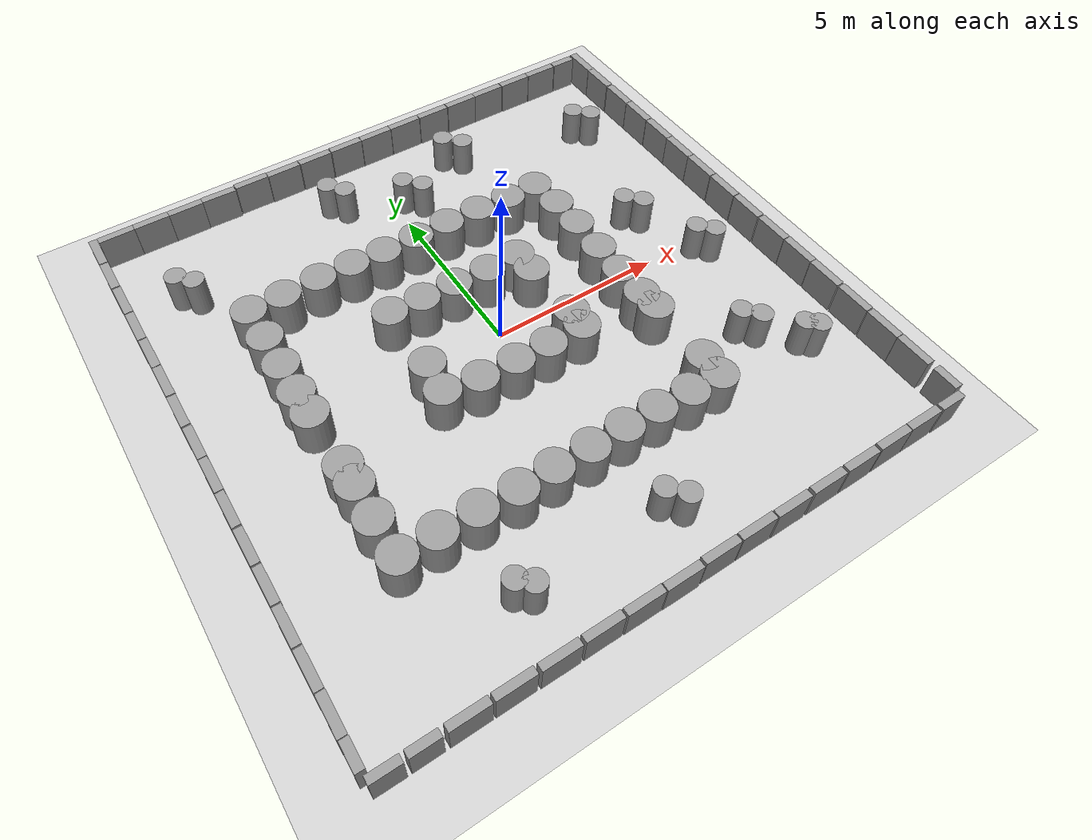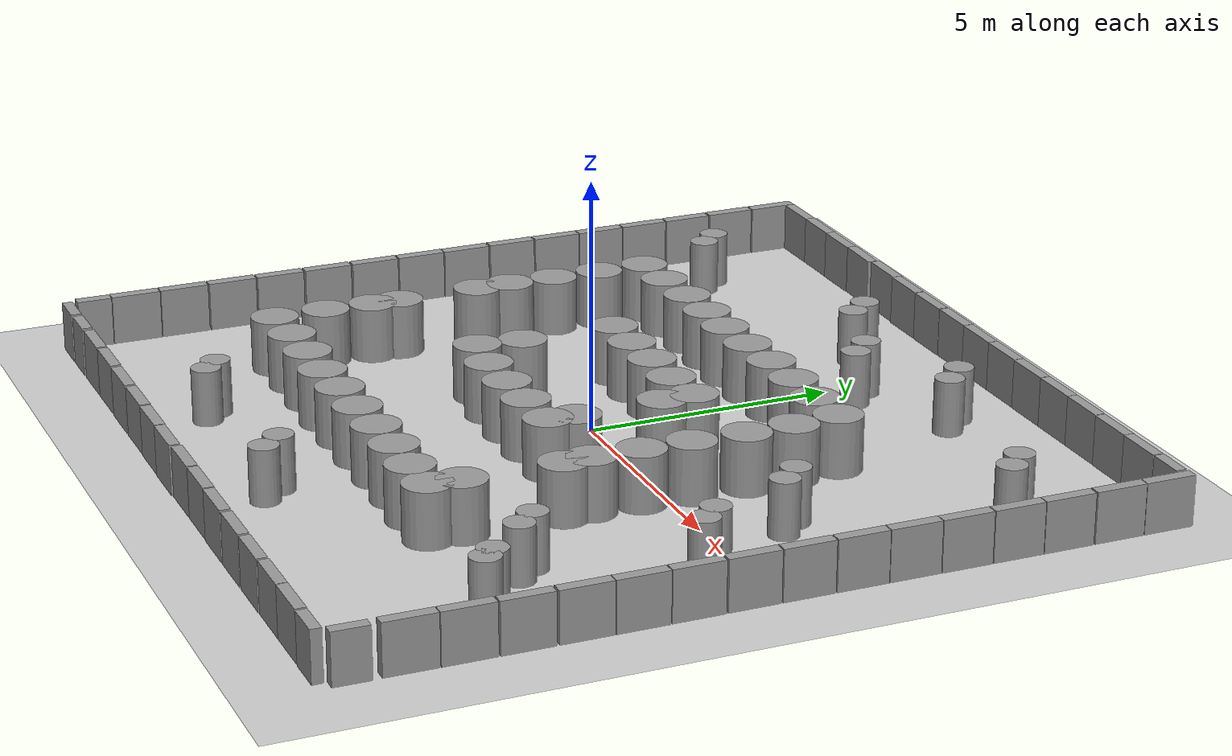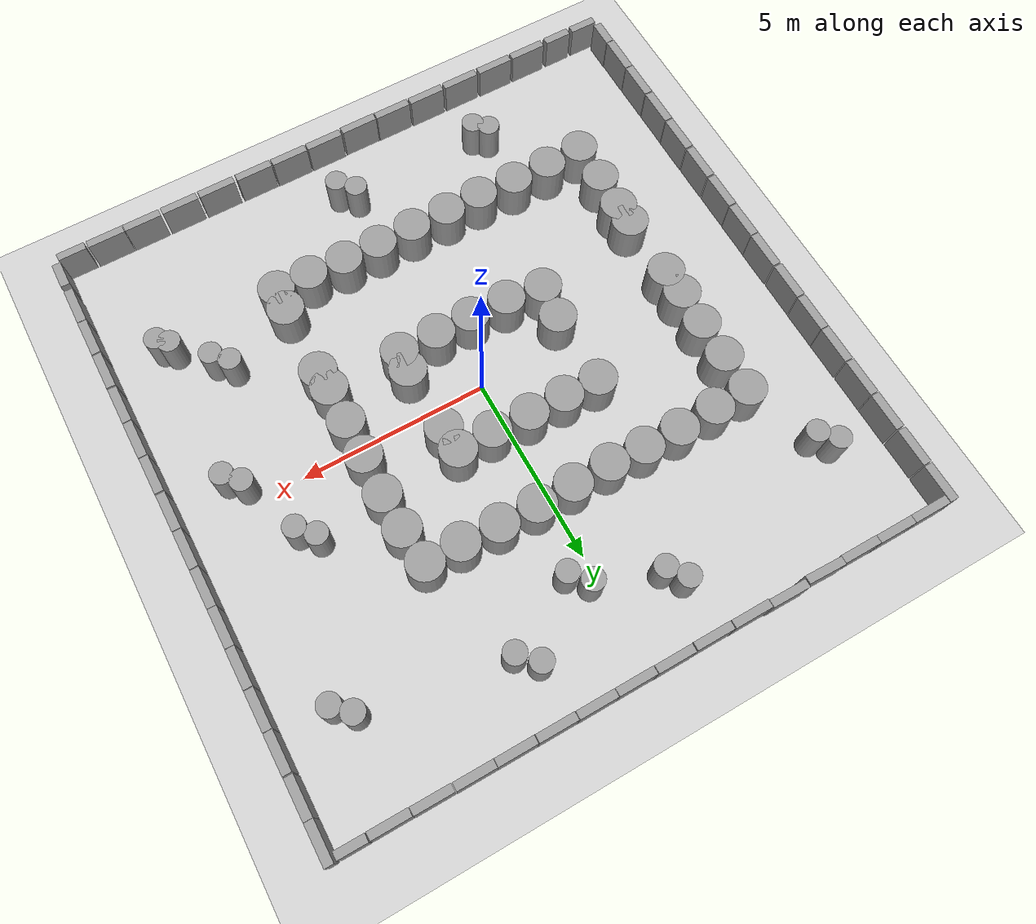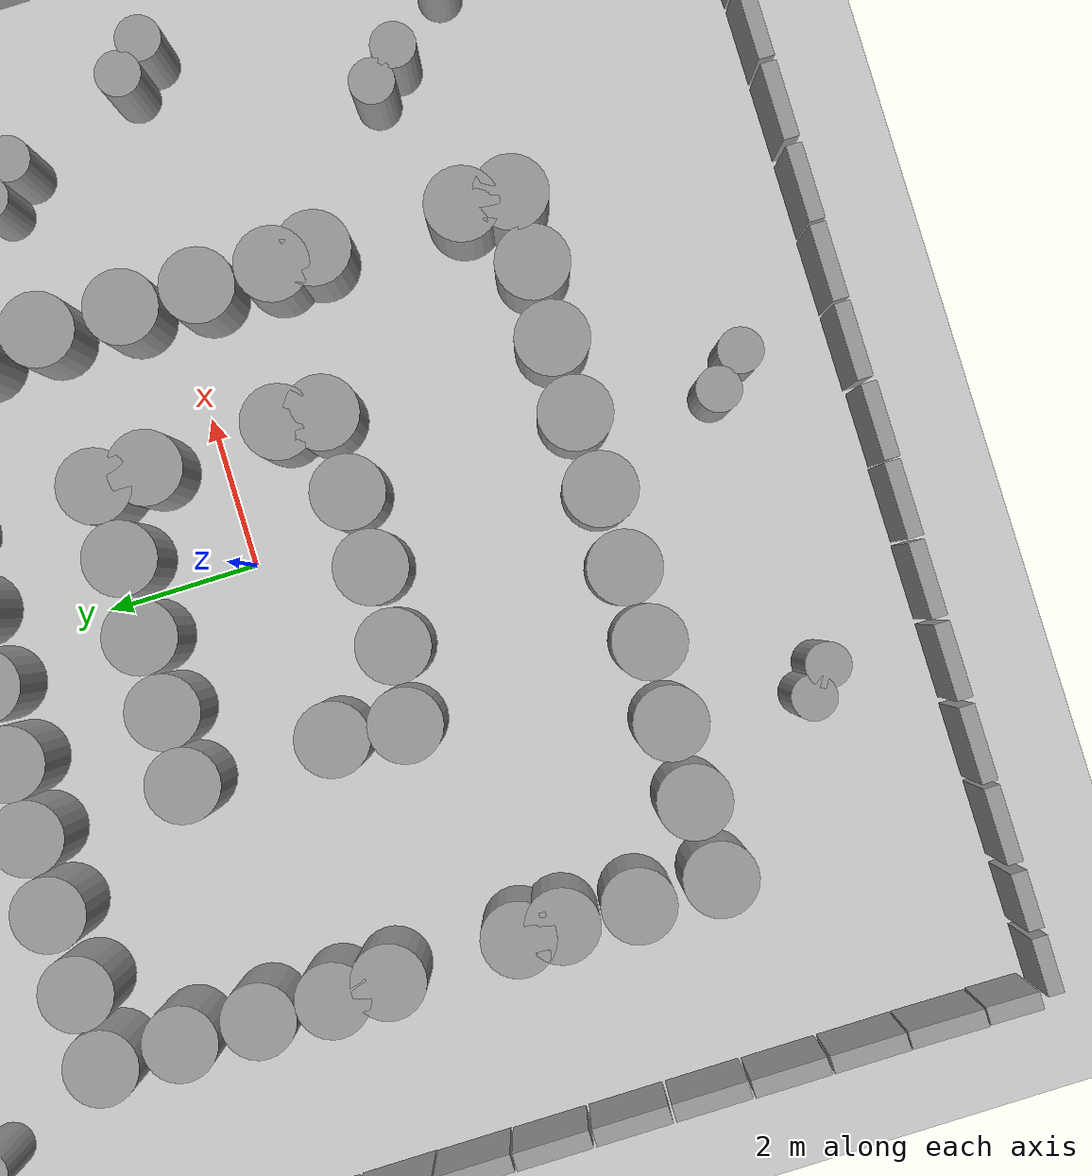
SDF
<sdf version="1.6">
 <world name="default">
  <light name="sun" type="directional">
   <pose>0 0 10 0 -0 0</pose>
   <diffuse>0.8 0.8 0.8 1</diffuse>
   <specular>0.1 0.1 0.1 1</specular>
   <attenuation>
    <range>1000</range>
    <constant>0.9</constant>
    <linear>0.01</linear>
    <quadratic>0.001</quadratic>
   </attenuation>
   <direction>-0.5 0.5 -1</direction>
  </light>
  <model name="ground_plane">
   <static>1</static>
   <static>1</static>
   <link name="link">
    <collision name="collision">
     <geometry><plane><normal>0 0 1</normal><size>100 100</size></plane></geometry>
     <surface><friction><ode><mu>100</mu><mu2>50</mu2></ode></friction></surface>
    </collision>
    <visual name="visual">
     <cast_shadows>0</cast_shadows>
     <geometry><plane><normal>0 0 1</normal><size>100 100</size></plane></geometry>
     <material>
      <script><uri>file://media/materials/scripts/gazebo.material</uri><name>Gazebo/Grey</name></script>
     </material>
    </visual>
   </link>
  </model>
  <gravity>0 0 -9.8</gravity>
  <magnetic_field>6e-06 2.3e-05 -4.2e-05</magnetic_field>
  <atmosphere type="adiabatic"/>
  <physics name="default_physics" default="0" type="ode">
   <max_step_size>0.001</max_step_size>
   <real_time_factor>1</real_time_factor>
   <real_time_update_rate>1000</real_time_update_rate>
  </physics>
  <scene><ambient>0.4 0.4 0.4 1</ambient><background>0.7 0.7 0.7 1</background><shadows>1</shadows></scene>
  <spherical_coordinates>
   <surface_model>EARTH_WGS84</surface_model>
   <latitude_deg>0</latitude_deg>
   <longitude_deg>0</longitude_deg>
   <elevation>0</elevation>
   <heading_deg>0</heading_deg>
  </spherical_coordinates>
  <audio><device>default</device></audio>
  <model name="unit_box_clone">
   <pose>-7.49845 8.11982 0.499998 0 5e-06 0.000244</pose>
   <link name="link">
    <inertial>
     <mass>1</mass>
     <inertia>
      <ixx>0.166667</ixx>
      <ixy>0</ixy>
      <ixz>0</ixz>
      <iyy>0.166667</iyy>
      <iyz>0</iyz>
      <izz>0.166667</izz>
     </inertia>
    </inertial>
    <collision name="collision"><geometry><box><size>1 0.210541 1</size></box></geometry></collision>
    <visual name="visual">
     <geometry><box><size>1 0.210541 1</size></box></geometry>
     <material>
      <script><name>Gazebo/Grey</name><uri>file://media/materials/scripts/gazebo.material</uri></script>
     </material>
    </visual>
   </link>
  </model>
  <model name="unit_box_clone_0">
   <pose>-6.49721 8.11971 0.5 0 0 -0.00255</pose>
   <link name="link">
    <inertial>
     <mass>1</mass>
     <inertia>
      <ixx>0.166667</ixx>
      <ixy>0</ixy>
      <ixz>0</ixz>
      <iyy>0.166667</iyy>
      <iyz>0</iyz>
      <izz>0.166667</izz>
     </inertia>
    </inertial>
    <collision name="collision"><geometry><box><size>1 0.210541 1</size></box></geometry></collision>
    <visual name="visual">
     <geometry><box><size>1 0.210541 1</size></box></geometry>
     <material>
      <script><name>Gazebo/Grey</name><uri>file://media/materials/scripts/gazebo.material</uri></script>
     </material>
    </visual>
   </link>
  </model>
  <model name="unit_box_clone_1">
   <pose>-5.49723 8.10829 0.5 0 0 -0.00255</pose>
   <link name="link">
    <inertial>
     <mass>1</mass>
     <inertia>
      <ixx>0.166667</ixx>
      <ixy>0</ixy>
      <ixz>0</ixz>
      <iyy>0.166667</iyy>
      <iyz>0</iyz>
      <izz>0.166667</izz>
     </inertia>
    </inertial>
    <collision name="collision"><geometry><box><size>1 0.210541 1</size></box></geometry></collision>
    <visual name="visual">
     <geometry><box><size>1 0.210541 1</size></box></geometry>
     <material>
      <script><name>Gazebo/Grey</name><uri>file://media/materials/scripts/gazebo.material</uri></script>
     </material>
    </visual>
   </link>
  </model>
  <model name="unit_box_clone_2">
   <pose>-4.49475 8.11073 0.499999 -1e-06 2e-06 -0.027192</pose>
   <link name="link">
    <inertial>
     <mass>1</mass>
     <inertia>
      <ixx>0.166667</ixx>
      <ixy>0</ixy>
      <ixz>0</ixz>
      <iyy>0.166667</iyy>
      <iyz>0</iyz>
      <izz>0.166667</izz>
     </inertia>
    </inertial>
    <collision name="collision"><geometry><box><size>1 0.210541 1</size></box></geometry></collision>
    <visual name="visual">
     <geometry><box><size>1 0.210541 1</size></box></geometry>
     <material>
      <script><name>Gazebo/Grey</name><uri>file://media/materials/scripts/gazebo.material</uri></script>
     </material>
    </visual>
   </link>
  </model>
  <model name="unit_box_clone_3">
   <pose>-3.46831 8.14903 0.499999 1e-06 2e-06 -0.008519</pose>
   <link name="link">
    <inertial>
     <mass>1</mass>
     <inertia>
      <ixx>0.166667</ixx>
      <ixy>0</ixy>
      <ixz>0</ixz>
      <iyy>0.166667</iyy>
      <iyz>0</iyz>
      <izz>0.166667</izz>
     </inertia>
    </inertial>
    <collision name="collision"><geometry><box><size>1 0.210541 1</size></box></geometry></collision>
    <visual name="visual">
     <geometry><box><size>1 0.210541 1</size></box></geometry>
     <material>
      <script><name>Gazebo/Grey</name><uri>file://media/materials/scripts/gazebo.material</uri></script>
     </material>
    </visual>
   </link>
  </model>
  <model name="unit_box_clone_4">
   <pose>-2.46316 8.11851 0.499998 0 5e-06 0.000244</pose>
   <link name="link">
    <inertial>
     <mass>1</mass>
     <inertia>
      <ixx>0.166667</ixx>
      <ixy>0</ixy>
      <ixz>0</ixz>
      <iyy>0.166667</iyy>
      <iyz>0</iyz>
      <izz>0.166667</izz>
     </inertia>
    </inertial>
    <collision name="collision"><geometry><box><size>1 0.210541 1</size></box></geometry></collision>
    <visual name="visual">
     <geometry><box><size>1 0.210541 1</size></box></geometry>
     <material>
      <script><name>Gazebo/Grey</name><uri>file://media/materials/scripts/gazebo.material</uri></script>
     </material>
    </visual>
   </link>
  </model>
  <model name="unit_box_clone_5">
   <pose>-1.44425 8.11185 0.499998 0 5e-06 0.000244</pose>
   <link name="link">
    <inertial>
     <mass>1</mass>
     <inertia>
      <ixx>0.166667</ixx>
      <ixy>0</ixy>
      <ixz>0</ixz>
      <iyy>0.166667</iyy>
      <iyz>0</iyz>
      <izz>0.166667</izz>
     </inertia>
    </inertial>
    <collision name="collision"><geometry><box><size>1 0.210541 1</size></box></geometry></collision>
    <visual name="visual">
     <geometry><box><size>1 0.210541 1</size></box></geometry>
     <material>
      <script><name>Gazebo/Grey</name><uri>file://media/materials/scripts/gazebo.material</uri></script>
     </material>
    </visual>
   </link>
  </model>
  <model name="unit_box_clone_6">
   <pose>-0.418678 8.1185 0.499998 0 5e-06 0.000244</pose>
   <link name="link">
    <inertial>
     <mass>1</mass>
     <inertia>
      <ixx>0.166667</ixx>
      <ixy>0</ixy>
      <ixz>0</ixz>
      <iyy>0.166667</iyy>
      <iyz>0</iyz>
      <izz>0.166667</izz>
     </inertia>
    </inertial>
    <collision name="collision"><geometry><box><size>1 0.210541 1</size></box></geometry></collision>
    <visual name="visual">
     <geometry><box><size>1 0.210541 1</size></box></geometry>
     <material>
      <script><name>Gazebo/Grey</name><uri>file://media/materials/scripts/gazebo.material</uri></script>
     </material>
    </visual>
   </link>
  </model>
  <model name="unit_box_clone_7">
   <pose>0.592841 8.11137 0.499998 0 5e-06 0.000244</pose>
   <link name="link">
    <inertial>
     <mass>1</mass>
     <inertia>
      <ixx>0.166667</ixx>
      <ixy>0</ixy>
      <ixz>0</ixz>
      <iyy>0.166667</iyy>
      <iyz>0</iyz>
      <izz>0.166667</izz>
     </inertia>
    </inertial>
    <collision name="collision"><geometry><box><size>1 0.210541 1</size></box></geometry></collision>
    <visual name="visual">
     <geometry><box><size>1 0.210541 1</size></box></geometry>
     <material>
      <script><name>Gazebo/Grey</name><uri>file://media/materials/scripts/gazebo.material</uri></script>
     </material>
    </visual>
   </link>
  </model>
  <model name="unit_box_clone_8">
   <pose>1.60043 8.10988 0.499998 0 5e-06 0.000244</pose>
   <link name="link">
    <inertial>
     <mass>1</mass>
     <inertia>
      <ixx>0.166667</ixx>
      <ixy>0</ixy>
      <ixz>0</ixz>
      <iyy>0.166667</iyy>
      <iyz>0</iyz>
      <izz>0.166667</izz>
     </inertia>
    </inertial>
    <collision name="collision"><geometry><box><size>1 0.210541 1</size></box></geometry></collision>
    <visual name="visual">
     <geometry><box><size>1 0.210541 1</size></box></geometry>
     <material>
      <script><name>Gazebo/Grey</name><uri>file://media/materials/scripts/gazebo.material</uri></script>
     </material>
    </visual>
   </link>
  </model>
  <model name="unit_box_clone_9">
   <pose>2.60987 8.10269 0.499998 0 5e-06 0.000244</pose>
   <link name="link">
    <inertial>
     <mass>1</mass>
     <inertia>
      <ixx>0.166667</ixx>
      <ixy>0</ixy>
      <ixz>0</ixz>
      <iyy>0.166667</iyy>
      <iyz>0</iyz>
      <izz>0.166667</izz>
     </inertia>
    </inertial>
    <collision name="collision"><geometry><box><size>1 0.210541 1</size></box></geometry></collision>
    <visual name="visual">
     <geometry><box><size>1 0.210541 1</size></box></geometry>
     <material>
      <script><name>Gazebo/Grey</name><uri>file://media/materials/scripts/gazebo.material</uri></script>
     </material>
    </visual>
   </link>
  </model>
  <model name="unit_box_clone_10">
   <pose>3.62649 8.0991 0.499998 0 5e-06 0.000244</pose>
   <link name="link">
    <inertial>
     <mass>1</mass>
     <inertia>
      <ixx>0.166667</ixx>
      <ixy>0</ixy>
      <ixz>0</ixz>
      <iyy>0.166667</iyy>
      <iyz>0</iyz>
      <izz>0.166667</izz>
     </inertia>
    </inertial>
    <collision name="collision"><geometry><box><size>1 0.210541 1</size></box></geometry></collision>
    <visual name="visual">
     <geometry><box><size>1 0.210541 1</size></box></geometry>
     <material>
      <script><name>Gazebo/Grey</name><uri>file://media/materials/scripts/gazebo.material</uri></script>
     </material>
    </visual>
   </link>
  </model>
  <model name="unit_box_clone_11">
   <pose>4.63311 8.09541 0.499998 -0 -5e-06 -0.003164</pose>
   <link name="link">
    <inertial>
     <mass>1</mass>
     <inertia>
      <ixx>0.166667</ixx>
      <ixy>0</ixy>
      <ixz>0</ixz>
      <iyy>0.166667</iyy>
      <iyz>0</iyz>
      <izz>0.166667</izz>
     </inertia>
    </inertial>
    <collision name="collision"><geometry><box><size>1 0.210541 1</size></box></geometry></collision>
    <visual name="visual">
     <geometry><box><size>1 0.210541 1</size></box></geometry>
     <material>
      <script><name>Gazebo/Grey</name><uri>file://media/materials/scripts/gazebo.material</uri></script>
     </material>
    </visual>
   </link>
  </model>
  <model name="unit_box_0_clone_0">
   <pose>8.11522 6.68459 0.5 0 -0 -0.000401</pose>
   <link name="link">
    <inertial>
     <mass>1</mass>
     <inertia>
      <ixx>0.166667</ixx>
      <ixy>0</ixy>
      <ixz>0</ixz>
      <iyy>0.166667</iyy>
      <iyz>0</iyz>
      <izz>0.166667</izz>
     </inertia>
    </inertial>
    <collision name="collision"><geometry><box><size>0.230819 1 1</size></box></geometry></collision>
    <visual name="visual">
     <geometry><box><size>0.230819 1 1</size></box></geometry>
     <material>
      <script><name>Gazebo/Grey</name><uri>file://media/materials/scripts/gazebo.material</uri></script>
     </material>
    </visual>
   </link>
  </model>
  <model name="unit_box_0_clone_1">
   <pose>8.11915 5.6517 0.5 0 -0 0.00028</pose>
   <link name="link">
    <inertial>
     <mass>1</mass>
     <inertia>
      <ixx>0.166667</ixx>
      <ixy>0</ixy>
      <ixz>0</ixz>
      <iyy>0.166667</iyy>
      <iyz>0</iyz>
      <izz>0.166667</izz>
     </inertia>
    </inertial>
    <collision name="collision"><geometry><box><size>0.230819 1 1</size></box></geometry></collision>
    <visual name="visual">
     <geometry><box><size>0.230819 1 1</size></box></geometry>
     <material>
      <script><name>Gazebo/Grey</name><uri>file://media/materials/scripts/gazebo.material</uri></script>
     </material>
    </visual>
   </link>
  </model>
  <model name="unit_box_0_clone_2">
   <pose>8.11914 4.64015 0.5 0 -0 0.000171</pose>
   <link name="link">
    <inertial>
     <mass>1</mass>
     <inertia>
      <ixx>0.166667</ixx>
      <ixy>0</ixy>
      <ixz>0</ixz>
      <iyy>0.166667</iyy>
      <iyz>0</iyz>
      <izz>0.166667</izz>
     </inertia>
    </inertial>
    <collision name="collision"><geometry><box><size>0.230819 1 1</size></box></geometry></collision>
    <visual name="visual">
     <geometry><box><size>0.230819 1 1</size></box></geometry>
     <material>
      <script><name>Gazebo/Grey</name><uri>file://media/materials/scripts/gazebo.material</uri></script>
     </material>
    </visual>
   </link>
  </model>
  <model name="unit_box_0_clone_3">
   <pose>8.11914 3.62225 0.5 0 -0 0.000152</pose>
   <link name="link">
    <inertial>
     <mass>1</mass>
     <inertia>
      <ixx>0.166667</ixx>
      <ixy>0</ixy>
      <ixz>0</ixz>
      <iyy>0.166667</iyy>
      <iyz>0</iyz>
      <izz>0.166667</izz>
     </inertia>
    </inertial>
    <collision name="collision"><geometry><box><size>0.230819 1 1</size></box></geometry></collision>
    <visual name="visual">
     <geometry><box><size>0.230819 1 1</size></box></geometry>
     <material>
      <script><name>Gazebo/Grey</name><uri>file://media/materials/scripts/gazebo.material</uri></script>
     </material>
    </visual>
   </link>
  </model>
  <model name="unit_box_0_clone_4">
   <pose>8.11332 2.61062 0.5 -1e-06 1e-06 -0.001351</pose>
   <link name="link">
    <inertial>
     <mass>1</mass>
     <inertia>
      <ixx>0.166667</ixx>
      <ixy>0</ixy>
      <ixz>0</ixz>
      <iyy>0.166667</iyy>
      <iyz>0</iyz>
      <izz>0.166667</izz>
     </inertia>
    </inertial>
    <collision name="collision"><geometry><box><size>0.230819 1 1</size></box></geometry></collision>
    <visual name="visual">
     <geometry><box><size>0.230819 1 1</size></box></geometry>
     <material>
      <script><name>Gazebo/Grey</name><uri>file://media/materials/scripts/gazebo.material</uri></script>
     </material>
    </visual>
   </link>
  </model>
  <model name="unit_box_0_clone_5">
   <pose>8.11277 1.59918 0.5 0 -0 0.000152</pose>
   <link name="link">
    <inertial>
     <mass>1</mass>
     <inertia>
      <ixx>0.166667</ixx>
      <ixy>0</ixy>
      <ixz>0</ixz>
      <iyy>0.166667</iyy>
      <iyz>0</iyz>
      <izz>0.166667</izz>
     </inertia>
    </inertial>
    <collision name="collision"><geometry><box><size>0.230819 1 1</size></box></geometry></collision>
    <visual name="visual">
     <geometry><box><size>0.230819 1 1</size></box></geometry>
     <material>
      <script><name>Gazebo/Grey</name><uri>file://media/materials/scripts/gazebo.material</uri></script>
     </material>
    </visual>
   </link>
  </model>
  <model name="unit_box_0_clone_6">
   <pose>8.11277 0.574929 0.5 0 -0 0.000152</pose>
   <link name="link">
    <inertial>
     <mass>1</mass>
     <inertia>
      <ixx>0.166667</ixx>
      <ixy>0</ixy>
      <ixz>0</ixz>
      <iyy>0.166667</iyy>
      <iyz>0</iyz>
      <izz>0.166667</izz>
     </inertia>
    </inertial>
    <collision name="collision"><geometry><box><size>0.230819 1 1</size></box></geometry></collision>
    <visual name="visual">
     <geometry><box><size>0.230819 1 1</size></box></geometry>
     <material>
      <script><name>Gazebo/Grey</name><uri>file://media/materials/scripts/gazebo.material</uri></script>
     </material>
    </visual>
   </link>
  </model>
  <model name="unit_box_0_clone_7">
   <pose>8.11276 -0.449329 0.5 0 -0 0.000152</pose>
   <link name="link">
    <inertial>
     <mass>1</mass>
     <inertia>
      <ixx>0.166667</ixx>
      <ixy>0</ixy>
      <ixz>0</ixz>
      <iyy>0.166667</iyy>
      <iyz>0</iyz>
      <izz>0.166667</izz>
     </inertia>
    </inertial>
    <collision name="collision"><geometry><box><size>0.230819 1 1</size></box></geometry></collision>
    <visual name="visual">
     <geometry><box><size>0.230819 1 1</size></box></geometry>
     <material>
      <script><name>Gazebo/Grey</name><uri>file://media/materials/scripts/gazebo.material</uri></script>
     </material>
    </visual>
   </link>
  </model>
  <model name="unit_box_0_clone_8">
   <pose>8.11912 -1.48632 0.5 0 -0 0.000152</pose>
   <link name="link">
    <inertial>
     <mass>1</mass>
     <inertia>
      <ixx>0.166667</ixx>
      <ixy>0</ixy>
      <ixz>0</ixz>
      <iyy>0.166667</iyy>
      <iyz>0</iyz>
      <izz>0.166667</izz>
     </inertia>
    </inertial>
    <collision name="collision"><geometry><box><size>0.230819 1 1</size></box></geometry></collision>
    <visual name="visual">
     <geometry><box><size>0.230819 1 1</size></box></geometry>
     <material>
      <script><name>Gazebo/Grey</name><uri>file://media/materials/scripts/gazebo.material</uri></script>
     </material>
    </visual>
   </link>
  </model>
  <model name="unit_box_0_clone_9">
   <pose>8.12548 -2.50422 0.5 0 -0 0.000152</pose>
   <link name="link">
    <inertial>
     <mass>1</mass>
     <inertia>
      <ixx>0.166667</ixx>
      <ixy>0</ixy>
      <ixz>0</ixz>
      <iyy>0.166667</iyy>
      <iyz>0</iyz>
      <izz>0.166667</izz>
     </inertia>
    </inertial>
    <collision name="collision"><geometry><box><size>0.230819 1 1</size></box></geometry></collision>
    <visual name="visual">
     <geometry><box><size>0.230819 1 1</size></box></geometry>
     <material>
      <script><name>Gazebo/Grey</name><uri>file://media/materials/scripts/gazebo.material</uri></script>
     </material>
    </visual>
   </link>
  </model>
  <model name="unit_box_0_clone_10">
   <pose>8.12331 -3.52224 0.5 0 -0 0.000152</pose>
   <link name="link">
    <inertial>
     <mass>1</mass>
     <inertia>
      <ixx>0.166667</ixx>
      <ixy>0</ixy>
      <ixz>0</ixz>
      <iyy>0.166667</iyy>
      <iyz>0</iyz>
      <izz>0.166667</izz>
     </inertia>
    </inertial>
    <collision name="collision"><geometry><box><size>0.230819 1 1</size></box></geometry></collision>
    <visual name="visual">
     <geometry><box><size>0.230819 1 1</size></box></geometry>
     <material>
      <script><name>Gazebo/Grey</name><uri>file://media/materials/scripts/gazebo.material</uri></script>
     </material>
    </visual>
   </link>
  </model>
  <model name="unit_box_0_clone_11">
   <pose>8.1233 -4.56317 0.5 0 -0 0.000152</pose>
   <link name="link">
    <inertial>
     <mass>1</mass>
     <inertia>
      <ixx>0.166667</ixx>
      <ixy>0</ixy>
      <ixz>0</ixz>
      <iyy>0.166667</iyy>
      <iyz>0</iyz>
      <izz>0.166667</izz>
     </inertia>
    </inertial>
    <collision name="collision"><geometry><box><size>0.230819 1 1</size></box></geometry></collision>
    <visual name="visual">
     <geometry><box><size>0.230819 1 1</size></box></geometry>
     <material>
      <script><name>Gazebo/Grey</name><uri>file://media/materials/scripts/gazebo.material</uri></script>
     </material>
    </visual>
   </link>
  </model>
  <model name="unit_box_0_clone_12">
   <pose>8.11815 -5.59379 0.5 0 -0 0.000152</pose>
   <link name="link">
    <inertial>
     <mass>1</mass>
     <inertia>
      <ixx>0.166667</ixx>
      <ixy>0</ixy>
      <ixz>0</ixz>
      <iyy>0.166667</iyy>
      <iyz>0</iyz>
      <izz>0.166667</izz>
     </inertia>
    </inertial>
    <collision name="collision"><geometry><box><size>0.230819 1 1</size></box></geometry></collision>
    <visual name="visual">
     <geometry><box><size>0.230819 1 1</size></box></geometry>
     <material>
      <script><name>Gazebo/Grey</name><uri>file://media/materials/scripts/gazebo.material</uri></script>
     </material>
    </visual>
   </link>
  </model>
  <model name="unit_box_0_clone_13">
   <pose>8.11333 -6.60775 0.5 1e-06 -1e-06 -0.005519</pose>
   <link name="link">
    <inertial>
     <mass>1</mass>
     <inertia>
      <ixx>0.166667</ixx>
      <ixy>0</ixy>
      <ixz>0</ixz>
      <iyy>0.166667</iyy>
      <iyz>0</iyz>
      <izz>0.166667</izz>
     </inertia>
    </inertial>
    <collision name="collision"><geometry><box><size>0.230819 1 1</size></box></geometry></collision>
    <visual name="visual">
     <geometry><box><size>0.230819 1 1</size></box></geometry>
     <material>
      <script><name>Gazebo/Grey</name><uri>file://media/materials/scripts/gazebo.material</uri></script>
     </material>
    </visual>
   </link>
  </model>
  <model name="unit_box_clone_15_clone_0">
   <pose>6.71207 -8.13122 0.499998 0 5e-06 0.000244</pose>
   <link name="link">
    <inertial>
     <mass>1</mass>
     <inertia>
      <ixx>0.166667</ixx>
      <ixy>0</ixy>
      <ixz>0</ixz>
      <iyy>0.166667</iyy>
      <iyz>0</iyz>
      <izz>0.166667</izz>
     </inertia>
    </inertial>
    <collision name="collision"><geometry><box><size>1 0.210541 1</size></box></geometry></collision>
    <visual name="visual">
     <geometry><box><size>1 0.210541 1</size></box></geometry>
     <material>
      <script><name>Gazebo/Grey</name><uri>file://media/materials/scripts/gazebo.material</uri></script>
     </material>
    </visual>
   </link>
  </model>
  <model name="unit_box_clone_15_clone_1">
   <pose>5.69715 -8.13121 0.499998 0 5e-06 0.000244</pose>
   <link name="link">
    <inertial>
     <mass>1</mass>
     <inertia>
      <ixx>0.166667</ixx>
      <ixy>0</ixy>
      <ixz>0</ixz>
      <iyy>0.166667</iyy>
      <iyz>0</iyz>
      <izz>0.166667</izz>
     </inertia>
    </inertial>
    <collision name="collision"><geometry><box><size>1 0.210541 1</size></box></geometry></collision>
    <visual name="visual">
     <geometry><box><size>1 0.210541 1</size></box></geometry>
     <material>
      <script><name>Gazebo/Grey</name><uri>file://media/materials/scripts/gazebo.material</uri></script>
     </material>
    </visual>
   </link>
  </model>
  <model name="unit_box_clone_15_clone_2">
   <pose>4.63881 -8.13739 0.499998 0 5e-06 0.000244</pose>
   <link name="link">
    <inertial>
     <mass>1</mass>
     <inertia>
      <ixx>0.166667</ixx>
      <ixy>0</ixy>
      <ixz>0</ixz>
      <iyy>0.166667</iyy>
      <iyz>0</iyz>
      <izz>0.166667</izz>
     </inertia>
    </inertial>
    <collision name="collision"><geometry><box><size>1 0.210541 1</size></box></geometry></collision>
    <visual name="visual">
     <geometry><box><size>1 0.210541 1</size></box></geometry>
     <material>
      <script><name>Gazebo/Grey</name><uri>file://media/materials/scripts/gazebo.material</uri></script>
     </material>
    </visual>
   </link>
  </model>
  <model name="unit_box_clone_15_clone_3">
   <pose>3.57975 -8.13739 0.499998 0 5e-06 0.000244</pose>
   <link name="link">
    <inertial>
     <mass>1</mass>
     <inertia>
      <ixx>0.166667</ixx>
      <ixy>0</ixy>
      <ixz>0</ixz>
      <iyy>0.166667</iyy>
      <iyz>0</iyz>
      <izz>0.166667</izz>
     </inertia>
    </inertial>
    <collision name="collision"><geometry><box><size>1 0.210541 1</size></box></geometry></collision>
    <visual name="visual">
     <geometry><box><size>1 0.210541 1</size></box></geometry>
     <material>
      <script><name>Gazebo/Grey</name><uri>file://media/materials/scripts/gazebo.material</uri></script>
     </material>
    </visual>
   </link>
  </model>
  <model name="unit_box_clone_15_clone_4">
   <pose>2.49815 -8.13738 0.499998 0 5e-06 0.000244</pose>
   <link name="link">
    <inertial>
     <mass>1</mass>
     <inertia>
      <ixx>0.166667</ixx>
      <ixy>0</ixy>
      <ixz>0</ixz>
      <iyy>0.166667</iyy>
      <iyz>0</iyz>
      <izz>0.166667</izz>
     </inertia>
    </inertial>
    <collision name="collision"><geometry><box><size>1 0.210541 1</size></box></geometry></collision>
    <visual name="visual">
     <geometry><box><size>1 0.210541 1</size></box></geometry>
     <material>
      <script><name>Gazebo/Grey</name><uri>file://media/materials/scripts/gazebo.material</uri></script>
     </material>
    </visual>
   </link>
  </model>
  <model name="unit_box_clone_15_clone_5">
   <pose>1.46162 -8.12611 0.499998 0 5e-06 0.000244</pose>
   <link name="link">
    <inertial>
     <mass>1</mass>
     <inertia>
      <ixx>0.166667</ixx>
      <ixy>0</ixy>
      <ixz>0</ixz>
      <iyy>0.166667</iyy>
      <iyz>0</iyz>
      <izz>0.166667</izz>
     </inertia>
    </inertial>
    <collision name="collision"><geometry><box><size>1 0.210541 1</size></box></geometry></collision>
    <visual name="visual">
     <geometry><box><size>1 0.210541 1</size></box></geometry>
     <material>
      <script><name>Gazebo/Grey</name><uri>file://media/materials/scripts/gazebo.material</uri></script>
     </material>
    </visual>
   </link>
  </model>
  <model name="unit_box_clone_15_clone_6">
   <pose>0.425094 -8.1261 0.499998 0 5e-06 0.000244</pose>
   <link name="link">
    <inertial>
     <mass>1</mass>
     <inertia>
      <ixx>0.166667</ixx>
      <ixy>0</ixy>
      <ixz>0</ixz>
      <iyy>0.166667</iyy>
      <iyz>0</iyz>
      <izz>0.166667</izz>
     </inertia>
    </inertial>
    <collision name="collision"><geometry><box><size>1 0.210541 1</size></box></geometry></collision>
    <visual name="visual">
     <geometry><box><size>1 0.210541 1</size></box></geometry>
     <material>
      <script><name>Gazebo/Grey</name><uri>file://media/materials/scripts/gazebo.material</uri></script>
     </material>
    </visual>
   </link>
  </model>
  <model name="unit_box_clone_15_clone_7">
   <pose>-0.633968 -8.14865 0.499998 0 5e-06 0.000244</pose>
   <link name="link">
    <inertial>
     <mass>1</mass>
     <inertia>
      <ixx>0.166667</ixx>
      <ixy>0</ixy>
      <ixz>0</ixz>
      <iyy>0.166667</iyy>
      <iyz>0</iyz>
      <izz>0.166667</izz>
     </inertia>
    </inertial>
    <collision name="collision"><geometry><box><size>1 0.210541 1</size></box></geometry></collision>
    <visual name="visual">
     <geometry><box><size>1 0.210541 1</size></box></geometry>
     <material>
      <script><name>Gazebo/Grey</name><uri>file://media/materials/scripts/gazebo.material</uri></script>
     </material>
    </visual>
   </link>
  </model>
  <model name="unit_box_clone_15_clone_8">
   <pose>-1.65923 -8.13737 0.499998 0 5e-06 0.000244</pose>
   <link name="link">
    <inertial>
     <mass>1</mass>
     <inertia>
      <ixx>0.166667</ixx>
      <ixy>0</ixy>
      <ixz>0</ixz>
      <iyy>0.166667</iyy>
      <iyz>0</iyz>
      <izz>0.166667</izz>
     </inertia>
    </inertial>
    <collision name="collision"><geometry><box><size>1 0.210541 1</size></box></geometry></collision>
    <visual name="visual">
     <geometry><box><size>1 0.210541 1</size></box></geometry>
     <material>
      <script><name>Gazebo/Grey</name><uri>file://media/materials/scripts/gazebo.material</uri></script>
     </material>
    </visual>
   </link>
  </model>
  <model name="unit_box_clone_15_clone_9">
   <pose>-2.70703 -8.12612 0.499998 0 5e-06 0.000244</pose>
   <link name="link">
    <inertial>
     <mass>1</mass>
     <inertia>
      <ixx>0.166667</ixx>
      <ixy>0</ixy>
      <ixz>0</ixz>
      <iyy>0.166667</iyy>
      <iyz>0</iyz>
      <izz>0.166667</izz>
     </inertia>
    </inertial>
    <collision name="collision"><geometry><box><size>1 0.210541 1</size></box></geometry></collision>
    <visual name="visual">
     <geometry><box><size>1 0.210541 1</size></box></geometry>
     <material>
      <script><name>Gazebo/Grey</name><uri>file://media/materials/scripts/gazebo.material</uri></script>
     </material>
    </visual>
   </link>
  </model>
  <model name="unit_box_clone_15_clone_10">
   <pose>-3.77736 -8.12611 0.499998 0 5e-06 0.000244</pose>
   <link name="link">
    <inertial>
     <mass>1</mass>
     <inertia>
      <ixx>0.166667</ixx>
      <ixy>0</ixy>
      <ixz>0</ixz>
      <iyy>0.166667</iyy>
      <iyz>0</iyz>
      <izz>0.166667</izz>
     </inertia>
    </inertial>
    <collision name="collision"><geometry><box><size>1 0.210541 1</size></box></geometry></collision>
    <visual name="visual">
     <geometry><box><size>1 0.210541 1</size></box></geometry>
     <material>
      <script><name>Gazebo/Grey</name><uri>file://media/materials/scripts/gazebo.material</uri></script>
     </material>
    </visual>
   </link>
  </model>
  <model name="unit_box_clone_15_clone_11">
   <pose>-4.85896 -8.11485 0.499998 0 5e-06 0.000244</pose>
   <link name="link">
    <inertial>
     <mass>1</mass>
     <inertia>
      <ixx>0.166667</ixx>
      <ixy>0</ixy>
      <ixz>0</ixz>
      <iyy>0.166667</iyy>
      <iyz>0</iyz>
      <izz>0.166667</izz>
     </inertia>
    </inertial>
    <collision name="collision"><geometry><box><size>1 0.210541 1</size></box></geometry></collision>
    <visual name="visual">
     <geometry><box><size>1 0.210541 1</size></box></geometry>
     <material>
      <script><name>Gazebo/Grey</name><uri>file://media/materials/scripts/gazebo.material</uri></script>
     </material>
    </visual>
   </link>
  </model>
  <model name="unit_box_clone_15_clone_12">
   <pose>-5.91802 -8.11484 0.499998 0 5e-06 0.000244</pose>
   <link name="link">
    <inertial>
     <mass>1</mass>
     <inertia>
      <ixx>0.166667</ixx>
      <ixy>0</ixy>
      <ixz>0</ixz>
      <iyy>0.166667</iyy>
      <iyz>0</iyz>
      <izz>0.166667</izz>
     </inertia>
    </inertial>
    <collision name="collision"><geometry><box><size>1 0.210541 1</size></box></geometry></collision>
    <visual name="visual">
     <geometry><box><size>1 0.210541 1</size></box></geometry>
     <material>
      <script><name>Gazebo/Grey</name><uri>file://media/materials/scripts/gazebo.material</uri></script>
     </material>
    </visual>
   </link>
  </model>
  <model name="unit_box_0_clone_4_clone">
   <pose>-8.12647 7.71767 0.5 0 -0 0.000152</pose>
   <link name="link">
    <inertial>
     <mass>1</mass>
     <inertia>
      <ixx>0.166667</ixx>
      <ixy>0</ixy>
      <ixz>0</ixz>
      <iyy>0.166667</iyy>
      <iyz>0</iyz>
      <izz>0.166667</izz>
     </inertia>
    </inertial>
    <collision name="collision"><geometry><box><size>0.230819 1 1</size></box></geometry></collision>
    <visual name="visual">
     <geometry><box><size>0.230819 1 1</size></box></geometry>
     <material>
      <script><name>Gazebo/Grey</name><uri>file://media/materials/scripts/gazebo.material</uri></script>
     </material>
    </visual>
   </link>
  </model>
  <model name="unit_box_0_clone_4_clone_0">
   <pose>-8.13281 6.68713 0.5 0 -0 0.000152</pose>
   <link name="link">
    <inertial>
     <mass>1</mass>
     <inertia>
      <ixx>0.166667</ixx>
      <ixy>0</ixy>
      <ixz>0</ixz>
      <iyy>0.166667</iyy>
      <iyz>0</iyz>
      <izz>0.166667</izz>
     </inertia>
    </inertial>
    <collision name="collision"><geometry><box><size>0.230819 1 1</size></box></geometry></collision>
    <visual name="visual">
     <geometry><box><size>0.230819 1 1</size></box></geometry>
     <material>
      <script><name>Gazebo/Grey</name><uri>file://media/materials/scripts/gazebo.material</uri></script>
     </material>
    </visual>
   </link>
  </model>
  <model name="unit_box_0_clone_4_clone_1">
   <pose>-8.12606 5.64721 0.5 0 -0 0.000152</pose>
   <link name="link">
    <inertial>
     <mass>1</mass>
     <inertia>
      <ixx>0.166667</ixx>
      <ixy>0</ixy>
      <ixz>0</ixz>
      <iyy>0.166667</iyy>
      <iyz>0</iyz>
      <izz>0.166667</izz>
     </inertia>
    </inertial>
    <collision name="collision"><geometry><box><size>0.230819 1 1</size></box></geometry></collision>
    <visual name="visual">
     <geometry><box><size>0.230819 1 1</size></box></geometry>
     <material>
      <script><name>Gazebo/Grey</name><uri>file://media/materials/scripts/gazebo.material</uri></script>
     </material>
    </visual>
   </link>
  </model>
  <model name="unit_box_0_clone_4_clone_2">
   <pose>-8.12607 4.62079 0.5 0 -0 0.000152</pose>
   <link name="link">
    <inertial>
     <mass>1</mass>
     <inertia>
      <ixx>0.166667</ixx>
      <ixy>0</ixy>
      <ixz>0</ixz>
      <iyy>0.166667</iyy>
      <iyz>0</iyz>
      <izz>0.166667</izz>
     </inertia>
    </inertial>
    <collision name="collision"><geometry><box><size>0.230819 1 1</size></box></geometry></collision>
    <visual name="visual">
     <geometry><box><size>0.230819 1 1</size></box></geometry>
     <material>
      <script><name>Gazebo/Grey</name><uri>file://media/materials/scripts/gazebo.material</uri></script>
     </material>
    </visual>
   </link>
  </model>
  <model name="unit_box_0_clone_4_clone_3">
   <pose>-8.11932 3.59437 0.5 0 -0 0.000152</pose>
   <link name="link">
    <inertial>
     <mass>1</mass>
     <inertia>
      <ixx>0.166667</ixx>
      <ixy>0</ixy>
      <ixz>0</ixz>
      <iyy>0.166667</iyy>
      <iyz>0</iyz>
      <izz>0.166667</izz>
     </inertia>
    </inertial>
    <collision name="collision"><geometry><box><size>0.230819 1 1</size></box></geometry></collision>
    <visual name="visual">
     <geometry><box><size>0.230819 1 1</size></box></geometry>
     <material>
      <script><name>Gazebo/Grey</name><uri>file://media/materials/scripts/gazebo.material</uri></script>
     </material>
    </visual>
   </link>
  </model>
  <model name="unit_box_0_clone_4_clone_4">
   <pose>-8.11932 2.57471 0.5 0 -0 0.000152</pose>
   <link name="link">
    <inertial>
     <mass>1</mass>
     <inertia>
      <ixx>0.166667</ixx>
      <ixy>0</ixy>
      <ixz>0</ixz>
      <iyy>0.166667</iyy>
      <iyz>0</iyz>
      <izz>0.166667</izz>
     </inertia>
    </inertial>
    <collision name="collision"><geometry><box><size>0.230819 1 1</size></box></geometry></collision>
    <visual name="visual">
     <geometry><box><size>0.230819 1 1</size></box></geometry>
     <material>
      <script><name>Gazebo/Grey</name><uri>file://media/materials/scripts/gazebo.material</uri></script>
     </material>
    </visual>
   </link>
  </model>
  <model name="unit_box_0_clone_4_clone_5">
   <pose>-8.12608 1.54154 0.5 0 -0 0.000152</pose>
   <link name="link">
    <inertial>
     <mass>1</mass>
     <inertia>
      <ixx>0.166667</ixx>
      <ixy>0</ixy>
      <ixz>0</ixz>
      <iyy>0.166667</iyy>
      <iyz>0</iyz>
      <izz>0.166667</izz>
     </inertia>
    </inertial>
    <collision name="collision"><geometry><box><size>0.230819 1 1</size></box></geometry></collision>
    <visual name="visual">
     <geometry><box><size>0.230819 1 1</size></box></geometry>
     <material>
      <script><name>Gazebo/Grey</name><uri>file://media/materials/scripts/gazebo.material</uri></script>
     </material>
    </visual>
   </link>
  </model>
  <model name="unit_box_0_clone_4_clone_6">
   <pose>-8.11933 0.501621 0.5 0 -0 0.000152</pose>
   <link name="link">
    <inertial>
     <mass>1</mass>
     <inertia>
      <ixx>0.166667</ixx>
      <ixy>0</ixy>
      <ixz>0</ixz>
      <iyy>0.166667</iyy>
      <iyz>0</iyz>
      <izz>0.166667</izz>
     </inertia>
    </inertial>
    <collision name="collision"><geometry><box><size>0.230819 1 1</size></box></geometry></collision>
    <visual name="visual">
     <geometry><box><size>0.230819 1 1</size></box></geometry>
     <material>
      <script><name>Gazebo/Grey</name><uri>file://media/materials/scripts/gazebo.material</uri></script>
     </material>
    </visual>
   </link>
  </model>
  <model name="unit_box_0_clone_4_clone_7">
   <pose>-8.12609 -0.518043 0.5 0 -0 0.000152</pose>
   <link name="link">
    <inertial>
     <mass>1</mass>
     <inertia>
      <ixx>0.166667</ixx>
      <ixy>0</ixy>
      <ixz>0</ixz>
      <iyy>0.166667</iyy>
      <iyz>0</iyz>
      <izz>0.166667</izz>
     </inertia>
    </inertial>
    <collision name="collision"><geometry><box><size>0.230819 1 1</size></box></geometry></collision>
    <visual name="visual">
     <geometry><box><size>0.230819 1 1</size></box></geometry>
     <material>
      <script><name>Gazebo/Grey</name><uri>file://media/materials/scripts/gazebo.material</uri></script>
     </material>
    </visual>
   </link>
  </model>
  <model name="unit_box_0_clone_4_clone_8">
   <pose>-8.13284 -1.54447 0.5 0 -0 0.000152</pose>
   <link name="link">
    <inertial>
     <mass>1</mass>
     <inertia>
      <ixx>0.166667</ixx>
      <ixy>0</ixy>
      <ixz>0</ixz>
      <iyy>0.166667</iyy>
      <iyz>0</iyz>
      <izz>0.166667</izz>
     </inertia>
    </inertial>
    <collision name="collision"><geometry><box><size>0.230819 1 1</size></box></geometry></collision>
    <visual name="visual">
     <geometry><box><size>0.230819 1 1</size></box></geometry>
     <material>
      <script><name>Gazebo/Grey</name><uri>file://media/materials/scripts/gazebo.material</uri></script>
     </material>
    </visual>
   </link>
  </model>
  <model name="unit_box_0_clone_4_clone_9">
   <pose>-8.13285 -2.58439 0.5 0 -0 0.000152</pose>
   <link name="link">
    <inertial>
     <mass>1</mass>
     <inertia>
      <ixx>0.166667</ixx>
      <ixy>0</ixy>
      <ixz>0</ixz>
      <iyy>0.166667</iyy>
      <iyz>0</iyz>
      <izz>0.166667</izz>
     </inertia>
    </inertial>
    <collision name="collision"><geometry><box><size>0.230819 1 1</size></box></geometry></collision>
    <visual name="visual">
     <geometry><box><size>0.230819 1 1</size></box></geometry>
     <material>
      <script><name>Gazebo/Grey</name><uri>file://media/materials/scripts/gazebo.material</uri></script>
     </material>
    </visual>
   </link>
  </model>
  <model name="unit_box_0_clone_4_clone_10">
   <pose>-8.13285 -3.62431 0.5 0 -0 0.000152</pose>
   <link name="link">
    <inertial>
     <mass>1</mass>
     <inertia>
      <ixx>0.166667</ixx>
      <ixy>0</ixy>
      <ixz>0</ixz>
      <iyy>0.166667</iyy>
      <iyz>0</iyz>
      <izz>0.166667</izz>
     </inertia>
    </inertial>
    <collision name="collision"><geometry><box><size>0.230819 1 1</size></box></geometry></collision>
    <visual name="visual">
     <geometry><box><size>0.230819 1 1</size></box></geometry>
     <material>
      <script><name>Gazebo/Grey</name><uri>file://media/materials/scripts/gazebo.material</uri></script>
     </material>
    </visual>
   </link>
  </model>
  <model name="unit_box_0_clone_4_clone_11">
   <pose>-8.1396 -4.65748 0.5 0 -0 0.000152</pose>
   <link name="link">
    <inertial>
     <mass>1</mass>
     <inertia>
      <ixx>0.166667</ixx>
      <ixy>0</ixy>
      <ixz>0</ixz>
      <iyy>0.166667</iyy>
      <iyz>0</iyz>
      <izz>0.166667</izz>
     </inertia>
    </inertial>
    <collision name="collision"><geometry><box><size>0.230819 1 1</size></box></geometry></collision>
    <visual name="visual">
     <geometry><box><size>0.230819 1 1</size></box></geometry>
     <material>
      <script><name>Gazebo/Grey</name><uri>file://media/materials/scripts/gazebo.material</uri></script>
     </material>
    </visual>
   </link>
  </model>
  <model name="unit_box_0_clone_4_clone_12">
   <pose>-8.1396 -5.69065 0.5 0 -0 0.000152</pose>
   <link name="link">
    <inertial>
     <mass>1</mass>
     <inertia>
      <ixx>0.166667</ixx>
      <ixy>0</ixy>
      <ixz>0</ixz>
      <iyy>0.166667</iyy>
      <iyz>0</iyz>
      <izz>0.166667</izz>
     </inertia>
    </inertial>
    <collision name="collision"><geometry><box><size>0.230819 1 1</size></box></geometry></collision>
    <visual name="visual">
     <geometry><box><size>0.230819 1 1</size></box></geometry>
     <material>
      <script><name>Gazebo/Grey</name><uri>file://media/materials/scripts/gazebo.material</uri></script>
     </material>
    </visual>
   </link>
  </model>
  <model name="unit_box_0_clone_4_clone_13">
   <pose>-8.14113 -6.70873 0.5 -1e-06 1e-06 -0.009195</pose>
   <link name="link">
    <inertial>
     <mass>1</mass>
     <inertia>
      <ixx>0.166667</ixx>
      <ixy>0</ixy>
      <ixz>0</ixz>
      <iyy>0.166667</iyy>
      <iyz>0</iyz>
      <izz>0.166667</izz>
     </inertia>
    </inertial>
    <collision name="collision"><geometry><box><size>0.230819 1 1</size></box></geometry></collision>
    <visual name="visual">
     <geometry><box><size>0.230819 1 1</size></box></geometry>
     <material>
      <script><name>Gazebo/Grey</name><uri>file://media/materials/scripts/gazebo.material</uri></script>
     </material>
    </visual>
   </link>
  </model>
  <model name="unit_box_0_clone_0_clone">
   <pose>8.11438 7.69322 0.5 0 -0 0.000262</pose>
   <link name="link">
    <inertial>
     <mass>1</mass>
     <inertia>
      <ixx>0.166667</ixx>
      <ixy>0</ixy>
      <ixz>0</ixz>
      <iyy>0.166667</iyy>
      <iyz>0</iyz>
      <izz>0.166667</izz>
     </inertia>
    </inertial>
    <collision name="collision"><geometry><box><size>0.230819 1 1</size></box></geometry></collision>
    <visual name="visual">
     <geometry><box><size>0.230819 1 1</size></box></geometry>
     <material>
      <script><name>Gazebo/Grey</name><uri>file://media/materials/scripts/gazebo.material</uri></script>
     </material>
    </visual>
   </link>
  </model>
  <model name="unit_box_clone_11_clone">
   <pose>5.65439 8.08346 0.499998 0 -5e-06 -0.003129</pose>
   <link name="link">
    <inertial>
     <mass>1</mass>
     <inertia>
      <ixx>0.166667</ixx>
      <ixy>0</ixy>
      <ixz>0</ixz>
      <iyy>0.166667</iyy>
      <iyz>0</iyz>
      <izz>0.166667</izz>
     </inertia>
    </inertial>
    <collision name="collision"><geometry><box><size>1 0.210541 1</size></box></geometry></collision>
    <visual name="visual">
     <geometry><box><size>1 0.210541 1</size></box></geometry>
     <material>
      <script><name>Gazebo/Grey</name><uri>file://media/materials/scripts/gazebo.material</uri></script>
     </material>
    </visual>
   </link>
  </model>
  <model name="unit_box_clone_11_clone_0">
   <pose>6.66439 8.07326 0.499998 0 5e-06 -0.003232</pose>
   <link name="link">
    <inertial>
     <mass>1</mass>
     <inertia>
      <ixx>0.166667</ixx>
      <ixy>0</ixy>
      <ixz>0</ixz>
      <iyy>0.166667</iyy>
      <iyz>0</iyz>
      <izz>0.166667</izz>
     </inertia>
    </inertial>
    <collision name="collision"><geometry><box><size>1 0.210541 1</size></box></geometry></collision>
    <visual name="visual">
     <geometry><box><size>1 0.210541 1</size></box></geometry>
     <material>
      <script><name>Gazebo/Grey</name><uri>file://media/materials/scripts/gazebo.material</uri></script>
     </material>
    </visual>
   </link>
  </model>
  <model name="unit_box_clone_11_clone_1_clone">
   <pose>7.56437 8.07323 0.499997 -2e-06 8e-06 -0.005251</pose>
   <link name="link">
    <inertial>
     <mass>1</mass>
     <inertia>
      <ixx>0.166667</ixx>
      <ixy>0</ixy>
      <ixz>0</ixz>
      <iyy>0.166667</iyy>
      <iyz>0</iyz>
      <izz>0.166667</izz>
     </inertia>
    </inertial>
    <collision name="collision"><geometry><box><size>0.750223 0.210541 1</size></box></geometry></collision>
    <visual name="visual">
     <geometry><box><size>0.750223 0.210541 1</size></box></geometry>
     <material>
      <script><name>Gazebo/Grey</name><uri>file://media/materials/scripts/gazebo.material</uri></script>
     </material>
    </visual>
   </link>
  </model>
  <model name="unit_box_clone_11_clone_1_clone_0">
   <pose>-6.90881 -8.11956 0.499997 -3e-06 -8e-06 0.001349</pose>
   <link name="link">
    <inertial>
     <mass>1</mass>
     <inertia>
      <ixx>0.166667</ixx>
      <ixy>0</ixy>
      <ixz>0</ixz>
      <iyy>0.166667</iyy>
      <iyz>0</iyz>
      <izz>0.166667</izz>
     </inertia>
    </inertial>
    <collision name="collision"><geometry><box><size>0.750223 0.210541 1</size></box></geometry></collision>
    <visual name="visual">
     <geometry><box><size>0.750223 0.210541 1</size></box></geometry>
     <material>
      <script><name>Gazebo/Grey</name><uri>file://media/materials/scripts/gazebo.material</uri></script>
     </material>
    </visual>
   </link>
  </model>
  <model name="unit_box_0_clone_4_clone_13_clone_clone">
   <pose>-8.13833 -7.5766 0.499997 -6e-06 -2e-06 -0.011626</pose>
   <link name="link">
    <inertial>
     <mass>1</mass>
     <inertia>
      <ixx>0.166667</ixx>
      <ixy>0</ixy>
      <ixz>0</ixz>
      <iyy>0.166667</iyy>
      <iyz>0</iyz>
      <izz>0.166667</izz>
     </inertia>
    </inertial>
    <collision name="collision"><geometry><box><size>0.230819 0.700336 1</size></box></geometry></collision>
    <visual name="visual">
     <geometry><box><size>0.230819 0.700336 1</size></box></geometry>
     <material>
      <script><name>Gazebo/Grey</name><uri>file://media/materials/scripts/gazebo.material</uri></script>
     </material>
    </visual>
   </link>
  </model>
  <model name="unit_box_clone_11_clone_1_clone_0_clone">
   <pose>-7.75476 -8.122 0.499997 2e-06 -8e-06 -0.006025</pose>
   <link name="link">
    <inertial>
     <mass>1</mass>
     <inertia>
      <ixx>0.166667</ixx>
      <ixy>0</ixy>
      <ixz>0</ixz>
      <iyy>0.166667</iyy>
      <iyz>0</iyz>
      <izz>0.166667</izz>
     </inertia>
    </inertial>
    <collision name="collision"><geometry><box><size>0.750223 0.210541 1</size></box></geometry></collision>
    <visual name="visual">
     <geometry><box><size>0.750223 0.210541 1</size></box></geometry>
     <material>
      <script><name>Gazebo/Grey</name><uri>file://media/materials/scripts/gazebo.material</uri></script>
     </material>
    </visual>
   </link>
  </model>
  <model name="unit_box_clone_11_clone_1_clone_2">
   <pose>7.64249 -8.13927 0.499997 -2e-06 8e-06 0.00131</pose>
   <link name="link">
    <inertial>
     <mass>1</mass>
     <inertia>
      <ixx>0.166667</ixx>
      <ixy>0</ixy>
      <ixz>0</ixz>
      <iyy>0.166667</iyy>
      <iyz>0</iyz>
      <izz>0.166667</izz>
     </inertia>
    </inertial>
    <collision name="collision"><geometry><box><size>0.750223 0.210541 1</size></box></geometry></collision>
    <visual name="visual">
     <geometry><box><size>0.750223 0.210541 1</size></box></geometry>
     <material>
      <script><name>Gazebo/Grey</name><uri>file://media/materials/scripts/gazebo.material</uri></script>
     </material>
    </visual>
   </link>
  </model>
  <model name="unit_box_0_clone_4_clone_13_clone_clone_clone">
   <pose>8.11857 -7.62156 0.5 0 -1e-06 -0.010264</pose>
   <link name="link">
    <inertial>
     <mass>1</mass>
     <inertia>
      <ixx>0.166667</ixx>
      <ixy>0</ixy>
      <ixz>0</ixz>
      <iyy>0.166667</iyy>
      <iyz>0</iyz>
      <izz>0.166667</izz>
     </inertia>
    </inertial>
    <collision name="collision"><geometry><box><size>0.230819 0.700336 1</size></box></geometry></collision>
    <visual name="visual">
     <geometry><box><size>0.230819 0.700336 1</size></box></geometry>
     <material>
      <script><name>Gazebo/Grey</name><uri>file://media/materials/scripts/gazebo.material</uri></script>
     </material>
    </visual>
   </link>
  </model>
  <model name="unit_cylinder_153_clone_clone_5_clone_clone_13_clone_0_clone_29_clone_32_clone_0_clone_4_clone_46_clone_42_clone_clone_clone_3">
   <static>1</static>
   <pose>-0.503744 1.48551 0 0 -0 0</pose>
   <link name="link">
    <inertial>
     <mass>1</mass>
     <inertia><ixx>0.145833</ixx><ixy>0</ixy><ixz>0</ixz><iyy>0.145833</iyy><iyz>0</iyz><izz>0.125</izz></inertia>
    </inertial>
    <collision name="collision">
     <geometry><cylinder><radius>0.484115</radius><length>2.18667</length></cylinder></geometry>
    </collision>
    <visual name="visual">
     <geometry><cylinder><radius>0.484115</radius><length>2.18667</length></cylinder></geometry>
     <material>
      <script><name>Gazebo/Grey</name><uri>file://media/materials/scripts/gazebo.material</uri></script>
     </material>
    </visual>
   </link>
  </model>
  <model name="unit_cylinder_153_clone_clone_5_clone_clone_13_clone_0_clone_29_clone_32_clone_0_clone_4_clone_46_clone_42_clone_clone_clone_4_clone">
   <static>1</static>
   <pose>6.67507 -4.71981 0 0 -0 0</pose>
   <link name="link">
    <inertial>
     <mass>1</mass>
     <inertia><ixx>0.145833</ixx><ixy>0</ixy><ixz>0</ixz><iyy>0.145833</iyy><iyz>0</iyz><izz>0.125</izz></inertia>
    </inertial>
    <collision name="collision">
     <geometry><cylinder><radius>0.295479</radius><length>2.18667</length></cylinder></geometry>
    </collision>
    <visual name="visual">
     <geometry><cylinder><radius>0.295479</radius><length>2.18667</length></cylinder></geometry>
     <material>
      <script><name>Gazebo/Grey</name><uri>file://media/materials/scripts/gazebo.material</uri></script>
     </material>
    </visual>
   </link>
  </model>
  <model name="unit_cylinder_153_clone_clone_5_clone_clone_13_clone_0_clone_29_clone_32_clone_0_clone_4_clone_46_clone_42_clone_clone_clone_4_clone_0">
   <static>1</static>
   <pose>6.41207 -4.48776 0 0 -0 0</pose>
   <link name="link">
    <inertial>
     <mass>1</mass>
     <inertia><ixx>0.145833</ixx><ixy>0</ixy><ixz>0</ixz><iyy>0.145833</iyy><iyz>0</iyz><izz>0.125</izz></inertia>
    </inertial>
    <collision name="collision">
     <geometry><cylinder><radius>0.295479</radius><length>2.18667</length></cylinder></geometry>
    </collision>
    <visual name="visual">
     <geometry><cylinder><radius>0.295479</radius><length>2.18667</length></cylinder></geometry>
     <material>
      <script><name>Gazebo/Grey</name><uri>file://media/materials/scripts/gazebo.material</uri></script>
     </material>
    </visual>
   </link>
  </model>
  <model name="unit_cylinder_153_clone_clone_5_clone_clone_13_clone_0_clone_29_clone_32_clone_0_clone_4_clone_46_clone_42_clone_clone_clone_4_clone_1">
   <static>1</static>
   <pose>5.63854 -3.69876 0 0 -0 0</pose>
   <link name="link">
    <inertial>
     <mass>1</mass>
     <inertia><ixx>0.145833</ixx><ixy>0</ixy><ixz>0</ixz><iyy>0.145833</iyy><iyz>0</iyz><izz>0.125</izz></inertia>
    </inertial>
    <collision name="collision">
     <geometry><cylinder><radius>0.295479</radius><length>2.18667</length></cylinder></geometry>
    </collision>
    <visual name="visual">
     <geometry><cylinder><radius>0.295479</radius><length>2.18667</length></cylinder></geometry>
     <material>
      <script><name>Gazebo/Grey</name><uri>file://media/materials/scripts/gazebo.material</uri></script>
     </material>
    </visual>
   </link>
  </model>
  <model name="unit_cylinder_153_clone_clone_5_clone_clone_13_clone_0_clone_29_clone_32_clone_0_clone_4_clone_46_clone_42_clone_clone_clone_4_clone_2">
   <static>1</static>
   <pose>5.28272 -3.312 0 0 -0 0</pose>
   <link name="link">
    <inertial>
     <mass>1</mass>
     <inertia><ixx>0.145833</ixx><ixy>0</ixy><ixz>0</ixz><iyy>0.145833</iyy><iyz>0</iyz><izz>0.125</izz></inertia>
    </inertial>
    <collision name="collision">
     <geometry><cylinder><radius>0.295479</radius><length>2.18667</length></cylinder></geometry>
    </collision>
    <visual name="visual">
     <geometry><cylinder><radius>0.295479</radius><length>2.18667</length></cylinder></geometry>
     <material>
      <script><name>Gazebo/Grey</name><uri>file://media/materials/scripts/gazebo.material</uri></script>
     </material>
    </visual>
   </link>
  </model>
  <model name="unit_cylinder_153_clone_clone_5_clone_clone_13_clone_0_clone_29_clone_32_clone_0_clone_4_clone_46_clone_42_clone_clone_clone_3_clone">
   <static>1</static>
   <pose>-1.48031 1.48714 0 0 -0 0</pose>
   <link name="link">
    <inertial>
     <mass>1</mass>
     <inertia><ixx>0.145833</ixx><ixy>0</ixy><ixz>0</ixz><iyy>0.145833</iyy><iyz>0</iyz><izz>0.125</izz></inertia>
    </inertial>
    <collision name="collision">
     <geometry><cylinder><radius>0.484115</radius><length>2.18667</length></cylinder></geometry>
    </collision>
    <visual name="visual">
     <geometry><cylinder><radius>0.484115</radius><length>2.18667</length></cylinder></geometry>
     <material>
      <script><name>Gazebo/Grey</name><uri>file://media/materials/scripts/gazebo.material</uri></script>
     </material>
    </visual>
   </link>
  </model>
  <model name="unit_cylinder_153_clone_clone_5_clone_clone_13_clone_0_clone_29_clone_32_clone_0_clone_4_clone_46_clone_42_clone_clone_clone_3_clone_0">
   <static>1</static>
   <pose>-2.42709 1.51206 0 0 -0 0</pose>
   <link name="link">
    <inertial>
     <mass>1</mass>
     <inertia><ixx>0.145833</ixx><ixy>0</ixy><ixz>0</ixz><iyy>0.145833</iyy><iyz>0</iyz><izz>0.125</izz></inertia>
    </inertial>
    <collision name="collision">
     <geometry><cylinder><radius>0.484115</radius><length>2.18667</length></cylinder></geometry>
    </collision>
    <visual name="visual">
     <geometry><cylinder><radius>0.484115</radius><length>2.18667</length></cylinder></geometry>
     <material>
      <script><name>Gazebo/Grey</name><uri>file://media/materials/scripts/gazebo.material</uri></script>
     </material>
    </visual>
   </link>
  </model>
  <model name="unit_cylinder_153_clone_clone_5_clone_clone_13_clone_0_clone_29_clone_32_clone_0_clone_4_clone_46_clone_42_clone_clone_clone_3_clone_2">
   <static>1</static>
   <pose>-2.4271 -0.431337 0 0 -0 0</pose>
   <link name="link">
    <inertial>
     <mass>1</mass>
     <inertia><ixx>0.145833</ixx><ixy>0</ixy><ixz>0</ixz><iyy>0.145833</iyy><iyz>0</iyz><izz>0.125</izz></inertia>
    </inertial>
    <collision name="collision">
     <geometry><cylinder><radius>0.484115</radius><length>2.18667</length></cylinder></geometry>
    </collision>
    <visual name="visual">
     <geometry><cylinder><radius>0.484115</radius><length>2.18667</length></cylinder></geometry>
     <material>
      <script><name>Gazebo/Grey</name><uri>file://media/materials/scripts/gazebo.material</uri></script>
     </material>
    </visual>
   </link>
  </model>
  <model name="unit_cylinder_153_clone_clone_5_clone_clone_13_clone_0_clone_29_clone_32_clone_0_clone_4_clone_46_clone_42_clone_clone_clone_3_clone_3">
   <static>1</static>
   <pose>-2.52677 -1.35321 0 0 -0 0</pose>
   <link name="link">
    <inertial>
     <mass>1</mass>
     <inertia><ixx>0.145833</ixx><ixy>0</ixy><ixz>0</ixz><iyy>0.145833</iyy><iyz>0</iyz><izz>0.125</izz></inertia>
    </inertial>
    <collision name="collision">
     <geometry><cylinder><radius>0.484115</radius><length>2.18667</length></cylinder></geometry>
    </collision>
    <visual name="visual">
     <geometry><cylinder><radius>0.484115</radius><length>2.18667</length></cylinder></geometry>
     <material>
      <script><name>Gazebo/Grey</name><uri>file://media/materials/scripts/gazebo.material</uri></script>
     </material>
    </visual>
   </link>
  </model>
  <model name="unit_cylinder_153_clone_clone_5_clone_clone_13_clone_0_clone_29_clone_32_clone_0_clone_4_clone_46_clone_42_clone_clone_clone_3_clone_4">
   <static>1</static>
   <pose>-1.53871 -1.49764 0 0 -0 0</pose>
   <link name="link">
    <inertial>
     <mass>1</mass>
     <inertia><ixx>0.145833</ixx><ixy>0</ixy><ixz>0</ixz><iyy>0.145833</iyy><iyz>0</iyz><izz>0.125</izz></inertia>
    </inertial>
    <collision name="collision">
     <geometry><cylinder><radius>0.484115</radius><length>2.18667</length></cylinder></geometry>
    </collision>
    <visual name="visual">
     <geometry><cylinder><radius>0.484115</radius><length>2.18667</length></cylinder></geometry>
     <material>
      <script><name>Gazebo/Grey</name><uri>file://media/materials/scripts/gazebo.material</uri></script>
     </material>
    </visual>
   </link>
  </model>
  <model name="unit_cylinder_153_clone_clone_5_clone_clone_13_clone_0_clone_29_clone_32_clone_0_clone_4_clone_46_clone_42_clone_clone_clone_3_clone_5">
   <static>1</static>
   <pose>-0.516087 -1.5194 0 0 -0 0</pose>
   <link name="link">
    <inertial>
     <mass>1</mass>
     <inertia><ixx>0.145833</ixx><ixy>0</ixy><ixz>0</ixz><iyy>0.145833</iyy><iyz>0</iyz><izz>0.125</izz></inertia>
    </inertial>
    <collision name="collision">
     <geometry><cylinder><radius>0.484115</radius><length>2.18667</length></cylinder></geometry>
    </collision>
    <visual name="visual">
     <geometry><cylinder><radius>0.484115</radius><length>2.18667</length></cylinder></geometry>
     <material>
      <script><name>Gazebo/Grey</name><uri>file://media/materials/scripts/gazebo.material</uri></script>
     </material>
    </visual>
   </link>
  </model>
  <model name="unit_cylinder_153_clone_clone_5_clone_clone_13_clone_0_clone_29_clone_32_clone_0_clone_4_clone_46_clone_42_clone_clone_clone_3_clone_6">
   <static>1</static>
   <pose>0.463016 -1.51941 0 0 -0 0</pose>
   <link name="link">
    <inertial>
     <mass>1</mass>
     <inertia><ixx>0.145833</ixx><ixy>0</ixy><ixz>0</ixz><iyy>0.145833</iyy><iyz>0</iyz><izz>0.125</izz></inertia>
    </inertial>
    <collision name="collision">
     <geometry><cylinder><radius>0.484115</radius><length>2.18667</length></cylinder></geometry>
    </collision>
    <visual name="visual">
     <geometry><cylinder><radius>0.484115</radius><length>2.18667</length></cylinder></geometry>
     <material>
      <script><name>Gazebo/Grey</name><uri>file://media/materials/scripts/gazebo.material</uri></script>
     </material>
    </visual>
   </link>
  </model>
  <model name="unit_cylinder_153_clone_clone_5_clone_clone_13_clone_0_clone_29_clone_32_clone_0_clone_4_clone_46_clone_42_clone_clone_clone_3_clone_7">
   <static>1</static>
   <pose>0.506547 1.43966 0 0 -0 0</pose>
   <link name="link">
    <inertial>
     <mass>1</mass>
     <inertia><ixx>0.145833</ixx><ixy>0</ixy><ixz>0</ixz><iyy>0.145833</iyy><iyz>0</iyz><izz>0.125</izz></inertia>
    </inertial>
    <collision name="collision">
     <geometry><cylinder><radius>0.484115</radius><length>2.18667</length></cylinder></geometry>
    </collision>
    <visual name="visual">
     <geometry><cylinder><radius>0.484115</radius><length>2.18667</length></cylinder></geometry>
     <material>
      <script><name>Gazebo/Grey</name><uri>file://media/materials/scripts/gazebo.material</uri></script>
     </material>
    </visual>
   </link>
  </model>
  <model name="unit_cylinder_153_clone_clone_5_clone_clone_13_clone_0_clone_29_clone_32_clone_0_clone_4_clone_46_clone_42_clone_clone_clone_3_clone_8">
   <static>1</static>
   <pose>1.46389 1.48317 0 0 -0 0</pose>
   <link name="link">
    <inertial>
     <mass>1</mass>
     <inertia><ixx>0.145833</ixx><ixy>0</ixy><ixz>0</ixz><iyy>0.145833</iyy><iyz>0</iyz><izz>0.125</izz></inertia>
    </inertial>
    <collision name="collision">
     <geometry><cylinder><radius>0.484115</radius><length>2.18667</length></cylinder></geometry>
    </collision>
    <visual name="visual">
     <geometry><cylinder><radius>0.484115</radius><length>2.18667</length></cylinder></geometry>
     <material>
      <script><name>Gazebo/Grey</name><uri>file://media/materials/scripts/gazebo.material</uri></script>
     </material>
    </visual>
   </link>
  </model>
  <model name="unit_cylinder_153_clone_clone_5_clone_clone_13_clone_0_clone_29_clone_32_clone_0_clone_4_clone_46_clone_42_clone_clone_clone_3_clone_9">
   <static>1</static>
   <pose>1.50739 -1.49765 0 0 -0 0</pose>
   <link name="link">
    <inertial>
     <mass>1</mass>
     <inertia><ixx>0.145833</ixx><ixy>0</ixy><ixz>0</ixz><iyy>0.145833</iyy><iyz>0</iyz><izz>0.125</izz></inertia>
    </inertial>
    <collision name="collision">
     <geometry><cylinder><radius>0.484115</radius><length>2.18667</length></cylinder></geometry>
    </collision>
    <visual name="visual">
     <geometry><cylinder><radius>0.484115</radius><length>2.18667</length></cylinder></geometry>
     <material>
      <script><name>Gazebo/Grey</name><uri>file://media/materials/scripts/gazebo.material</uri></script>
     </material>
    </visual>
   </link>
  </model>
  <model name="unit_cylinder_153_clone_clone_5_clone_clone_13_clone_0_clone_29_clone_32_clone_0_clone_4_clone_46_clone_42_clone_clone_clone_3_clone_10">
   <static>1</static>
   <pose>-0.429072 -4.54374 0 0 -0 0</pose>
   <link name="link">
    <inertial>
     <mass>1</mass>
     <inertia><ixx>0.145833</ixx><ixy>0</ixy><ixz>0</ixz><iyy>0.145833</iyy><iyz>0</iyz><izz>0.125</izz></inertia>
    </inertial>
    <collision name="collision">
     <geometry><cylinder><radius>0.484115</radius><length>2.18667</length></cylinder></geometry>
    </collision>
    <visual name="visual">
     <geometry><cylinder><radius>0.484115</radius><length>2.18667</length></cylinder></geometry>
     <material>
      <script><name>Gazebo/Grey</name><uri>file://media/materials/scripts/gazebo.material</uri></script>
     </material>
    </visual>
   </link>
  </model>
  <model name="unit_cylinder_153_clone_clone_5_clone_clone_13_clone_0_clone_29_clone_32_clone_0_clone_4_clone_46_clone_42_clone_clone_clone_3_clone_11">
   <static>1</static>
   <pose>0.571789 -4.52199 0 0 -0 0</pose>
   <link name="link">
    <inertial>
     <mass>1</mass>
     <inertia><ixx>0.145833</ixx><ixy>0</ixy><ixz>0</ixz><iyy>0.145833</iyy><iyz>0</iyz><izz>0.125</izz></inertia>
    </inertial>
    <collision name="collision">
     <geometry><cylinder><radius>0.484115</radius><length>2.18667</length></cylinder></geometry>
    </collision>
    <visual name="visual">
     <geometry><cylinder><radius>0.484115</radius><length>2.18667</length></cylinder></geometry>
     <material>
      <script><name>Gazebo/Grey</name><uri>file://media/materials/scripts/gazebo.material</uri></script>
     </material>
    </visual>
   </link>
  </model>
  <model name="unit_cylinder_153_clone_clone_5_clone_clone_13_clone_0_clone_29_clone_32_clone_0_clone_4_clone_46_clone_42_clone_clone_clone_3_clone_12">
   <static>1</static>
   <pose>1.55089 -4.522 0 0 -0 0</pose>
   <link name="link">
    <inertial>
     <mass>1</mass>
     <inertia><ixx>0.145833</ixx><ixy>0</ixy><ixz>0</ixz><iyy>0.145833</iyy><iyz>0</iyz><izz>0.125</izz></inertia>
    </inertial>
    <collision name="collision">
     <geometry><cylinder><radius>0.484115</radius><length>2.18667</length></cylinder></geometry>
    </collision>
    <visual name="visual">
     <geometry><cylinder><radius>0.484115</radius><length>2.18667</length></cylinder></geometry>
     <material>
      <script><name>Gazebo/Grey</name><uri>file://media/materials/scripts/gazebo.material</uri></script>
     </material>
    </visual>
   </link>
  </model>
  <model name="unit_cylinder_153_clone_clone_5_clone_clone_13_clone_0_clone_29_clone_32_clone_0_clone_4_clone_46_clone_42_clone_clone_clone_3_clone_13">
   <static>1</static>
   <pose>2.52999 -4.56552 0 0 -0 0</pose>
   <link name="link">
    <inertial>
     <mass>1</mass>
     <inertia><ixx>0.145833</ixx><ixy>0</ixy><ixz>0</ixz><iyy>0.145833</iyy><iyz>0</iyz><izz>0.125</izz></inertia>
    </inertial>
    <collision name="collision">
     <geometry><cylinder><radius>0.484115</radius><length>2.18667</length></cylinder></geometry>
    </collision>
    <visual name="visual">
     <geometry><cylinder><radius>0.484115</radius><length>2.18667</length></cylinder></geometry>
     <material>
      <script><name>Gazebo/Grey</name><uri>file://media/materials/scripts/gazebo.material</uri></script>
     </material>
    </visual>
   </link>
  </model>
  <model name="unit_cylinder_153_clone_clone_5_clone_clone_13_clone_0_clone_29_clone_32_clone_0_clone_4_clone_46_clone_42_clone_clone_clone_3_clone_14">
   <static>1</static>
   <pose>3.44382 -4.56552 0 0 -0 0</pose>
   <link name="link">
    <inertial>
     <mass>1</mass>
     <inertia><ixx>0.145833</ixx><ixy>0</ixy><ixz>0</ixz><iyy>0.145833</iyy><iyz>0</iyz><izz>0.125</izz></inertia>
    </inertial>
    <collision name="collision">
     <geometry><cylinder><radius>0.484115</radius><length>2.18667</length></cylinder></geometry>
    </collision>
    <visual name="visual">
     <geometry><cylinder><radius>0.484115</radius><length>2.18667</length></cylinder></geometry>
     <material>
      <script><name>Gazebo/Grey</name><uri>file://media/materials/scripts/gazebo.material</uri></script>
     </material>
    </visual>
   </link>
  </model>
  <model name="unit_cylinder_153_clone_clone_5_clone_clone_13_clone_0_clone_29_clone_32_clone_0_clone_4_clone_46_clone_42_clone_clone_clone_3_clone_15">
   <static>1</static>
   <pose>-1.45169 -4.54374 0 0 -0 0</pose>
   <link name="link">
    <inertial>
     <mass>1</mass>
     <inertia><ixx>0.145833</ixx><ixy>0</ixy><ixz>0</ixz><iyy>0.145833</iyy><iyz>0</iyz><izz>0.125</izz></inertia>
    </inertial>
    <collision name="collision">
     <geometry><cylinder><radius>0.484115</radius><length>2.18667</length></cylinder></geometry>
    </collision>
    <visual name="visual">
     <geometry><cylinder><radius>0.484115</radius><length>2.18667</length></cylinder></geometry>
     <material>
      <script><name>Gazebo/Grey</name><uri>file://media/materials/scripts/gazebo.material</uri></script>
     </material>
    </visual>
   </link>
  </model>
  <model name="unit_cylinder_153_clone_clone_5_clone_clone_13_clone_0_clone_29_clone_32_clone_0_clone_4_clone_46_clone_42_clone_clone_clone_3_clone_16">
   <static>1</static>
   <pose>-2.43079 -4.56549 0 0 -0 0</pose>
   <link name="link">
    <inertial>
     <mass>1</mass>
     <inertia><ixx>0.145833</ixx><ixy>0</ixy><ixz>0</ixz><iyy>0.145833</iyy><iyz>0</iyz><izz>0.125</izz></inertia>
    </inertial>
    <collision name="collision">
     <geometry><cylinder><radius>0.484115</radius><length>2.18667</length></cylinder></geometry>
    </collision>
    <visual name="visual">
     <geometry><cylinder><radius>0.484115</radius><length>2.18667</length></cylinder></geometry>
     <material>
      <script><name>Gazebo/Grey</name><uri>file://media/materials/scripts/gazebo.material</uri></script>
     </material>
    </visual>
   </link>
  </model>
  <model name="unit_cylinder_153_clone_clone_5_clone_clone_13_clone_0_clone_29_clone_32_clone_0_clone_4_clone_46_clone_42_clone_clone_clone_3_clone_17">
   <static>1</static>
   <pose>-3.47517 -4.52197 0 0 -0 0</pose>
   <link name="link">
    <inertial>
     <mass>1</mass>
     <inertia><ixx>0.145833</ixx><ixy>0</ixy><ixz>0</ixz><iyy>0.145833</iyy><iyz>0</iyz><izz>0.125</izz></inertia>
    </inertial>
    <collision name="collision">
     <geometry><cylinder><radius>0.484115</radius><length>2.18667</length></cylinder></geometry>
    </collision>
    <visual name="visual">
     <geometry><cylinder><radius>0.484115</radius><length>2.18667</length></cylinder></geometry>
     <material>
      <script><name>Gazebo/Grey</name><uri>file://media/materials/scripts/gazebo.material</uri></script>
     </material>
    </visual>
   </link>
  </model>
  <model name="unit_cylinder_153_clone_clone_5_clone_clone_13_clone_0_clone_29_clone_32_clone_0_clone_4_clone_46_clone_42_clone_clone_clone_3_clone_18">
   <static>1</static>
   <pose>-4.49779 -4.51448 0 0 -0 0</pose>
   <link name="link">
    <inertial>
     <mass>1</mass>
     <inertia><ixx>0.145833</ixx><ixy>0</ixy><ixz>0</ixz><iyy>0.145833</iyy><iyz>0</iyz><izz>0.125</izz></inertia>
    </inertial>
    <collision name="collision">
     <geometry><cylinder><radius>0.484115</radius><length>2.18667</length></cylinder></geometry>
    </collision>
    <visual name="visual">
     <geometry><cylinder><radius>0.484115</radius><length>2.18667</length></cylinder></geometry>
     <material>
      <script><name>Gazebo/Grey</name><uri>file://media/materials/scripts/gazebo.material</uri></script>
     </material>
    </visual>
   </link>
  </model>
  <model name="unit_cylinder_153_clone_clone_5_clone_clone_13_clone_0_clone_29_clone_32_clone_0_clone_4_clone_46_clone_42_clone_clone_clone_3_clone_19">
   <static>1</static>
   <pose>-5.51133 -4.54302 0 0 -0 0</pose>
   <link name="link">
    <inertial>
     <mass>1</mass>
     <inertia><ixx>0.145833</ixx><ixy>0</ixy><ixz>0</ixz><iyy>0.145833</iyy><iyz>0</iyz><izz>0.125</izz></inertia>
    </inertial>
    <collision name="collision">
     <geometry><cylinder><radius>0.484115</radius><length>2.18667</length></cylinder></geometry>
    </collision>
    <visual name="visual">
     <geometry><cylinder><radius>0.484115</radius><length>2.18667</length></cylinder></geometry>
     <material>
      <script><name>Gazebo/Grey</name><uri>file://media/materials/scripts/gazebo.material</uri></script>
     </material>
    </visual>
   </link>
  </model>
  <model name="unit_cylinder_153_clone_clone_5_clone_clone_13_clone_0_clone_29_clone_32_clone_0_clone_4_clone_46_clone_42_clone_clone_clone_3_clone_20">
   <static>1</static>
   <pose>-5.5256 -3.47237 0 0 -0 0</pose>
   <link name="link">
    <inertial>
     <mass>1</mass>
     <inertia><ixx>0.145833</ixx><ixy>0</ixy><ixz>0</ixz><iyy>0.145833</iyy><iyz>0</iyz><izz>0.125</izz></inertia>
    </inertial>
    <collision name="collision">
     <geometry><cylinder><radius>0.484115</radius><length>2.18667</length></cylinder></geometry>
    </collision>
    <visual name="visual">
     <geometry><cylinder><radius>0.484115</radius><length>2.18667</length></cylinder></geometry>
     <material>
      <script><name>Gazebo/Grey</name><uri>file://media/materials/scripts/gazebo.material</uri></script>
     </material>
    </visual>
   </link>
  </model>
  <model name="unit_cylinder_153_clone_clone_5_clone_clone_13_clone_0_clone_29_clone_32_clone_0_clone_4_clone_46_clone_42_clone_clone_clone_3_clone_21">
   <static>1</static>
   <pose>-5.48277 -2.48738 0 0 -0 0</pose>
   <link name="link">
    <inertial>
     <mass>1</mass>
     <inertia><ixx>0.145833</ixx><ixy>0</ixy><ixz>0</ixz><iyy>0.145833</iyy><iyz>0</iyz><izz>0.125</izz></inertia>
    </inertial>
    <collision name="collision">
     <geometry><cylinder><radius>0.484115</radius><length>2.18667</length></cylinder></geometry>
    </collision>
    <visual name="visual">
     <geometry><cylinder><radius>0.484115</radius><length>2.18667</length></cylinder></geometry>
     <material>
      <script><name>Gazebo/Grey</name><uri>file://media/materials/scripts/gazebo.material</uri></script>
     </material>
    </visual>
   </link>
  </model>
  <model name="unit_cylinder_153_clone_clone_5_clone_clone_13_clone_0_clone_29_clone_32_clone_0_clone_4_clone_46_clone_42_clone_clone_clone_3_clone_22">
   <static>1</static>
   <pose>-5.48277 -1.91637 0 0 -0 0</pose>
   <link name="link">
    <inertial>
     <mass>1</mass>
     <inertia><ixx>0.145833</ixx><ixy>0</ixy><ixz>0</ixz><iyy>0.145833</iyy><iyz>0</iyz><izz>0.125</izz></inertia>
    </inertial>
    <collision name="collision">
     <geometry><cylinder><radius>0.484115</radius><length>2.18667</length></cylinder></geometry>
    </collision>
    <visual name="visual">
     <geometry><cylinder><radius>0.484115</radius><length>2.18667</length></cylinder></geometry>
     <material>
      <script><name>Gazebo/Grey</name><uri>file://media/materials/scripts/gazebo.material</uri></script>
     </material>
    </visual>
   </link>
  </model>
  <model name="unit_cylinder_153_clone_clone_5_clone_clone_13_clone_0_clone_29_clone_32_clone_0_clone_4_clone_46_clone_42_clone_clone_clone_3_clone_23">
   <static>1</static>
   <pose>-5.51131 -0.217603 0 0 -0 0</pose>
   <link name="link">
    <inertial>
     <mass>1</mass>
     <inertia><ixx>0.145833</ixx><ixy>0</ixy><ixz>0</ixz><iyy>0.145833</iyy><iyz>0</iyz><izz>0.125</izz></inertia>
    </inertial>
    <collision name="collision">
     <geometry><cylinder><radius>0.484115</radius><length>2.18667</length></cylinder></geometry>
    </collision>
    <visual name="visual">
     <geometry><cylinder><radius>0.484115</radius><length>2.18667</length></cylinder></geometry>
     <material>
      <script><name>Gazebo/Grey</name><uri>file://media/materials/scripts/gazebo.material</uri></script>
     </material>
    </visual>
   </link>
  </model>
  <model name="unit_cylinder_153_clone_clone_5_clone_clone_13_clone_0_clone_29_clone_32_clone_0_clone_4_clone_46_clone_42_clone_clone_clone_3_clone_24">
   <static>1</static>
   <pose>-5.52558 0.510438 0 0 -0 0</pose>
   <link name="link">
    <inertial>
     <mass>1</mass>
     <inertia><ixx>0.145833</ixx><ixy>0</ixy><ixz>0</ixz><iyy>0.145833</iyy><iyz>0</iyz><izz>0.125</izz></inertia>
    </inertial>
    <collision name="collision">
     <geometry><cylinder><radius>0.484115</radius><length>2.18667</length></cylinder></geometry>
    </collision>
    <visual name="visual">
     <geometry><cylinder><radius>0.484115</radius><length>2.18667</length></cylinder></geometry>
     <material>
      <script><name>Gazebo/Grey</name><uri>file://media/materials/scripts/gazebo.material</uri></script>
     </material>
    </visual>
   </link>
  </model>
  <model name="unit_cylinder_153_clone_clone_5_clone_clone_13_clone_0_clone_29_clone_32_clone_0_clone_4_clone_46_clone_42_clone_clone_clone_3_clone_25">
   <static>1</static>
   <pose>-5.49703 1.46688 0 0 -0 0</pose>
   <link name="link">
    <inertial>
     <mass>1</mass>
     <inertia><ixx>0.145833</ixx><ixy>0</ixy><ixz>0</ixz><iyy>0.145833</iyy><iyz>0</iyz><izz>0.125</izz></inertia>
    </inertial>
    <collision name="collision">
     <geometry><cylinder><radius>0.484115</radius><length>2.18667</length></cylinder></geometry>
    </collision>
    <visual name="visual">
     <geometry><cylinder><radius>0.484115</radius><length>2.18667</length></cylinder></geometry>
     <material>
      <script><name>Gazebo/Grey</name><uri>file://media/materials/scripts/gazebo.material</uri></script>
     </material>
    </visual>
   </link>
  </model>
  <model name="unit_cylinder_153_clone_clone_5_clone_clone_13_clone_0_clone_29_clone_32_clone_0_clone_4_clone_46_clone_42_clone_clone_clone_3_clone_26">
   <static>1</static>
   <pose>-5.48275 2.48043 0 0 -0 0</pose>
   <link name="link">
    <inertial>
     <mass>1</mass>
     <inertia><ixx>0.145833</ixx><ixy>0</ixy><ixz>0</ixz><iyy>0.145833</iyy><iyz>0</iyz><izz>0.125</izz></inertia>
    </inertial>
    <collision name="collision">
     <geometry><cylinder><radius>0.484115</radius><length>2.18667</length></cylinder></geometry>
    </collision>
    <visual name="visual">
     <geometry><cylinder><radius>0.484115</radius><length>2.18667</length></cylinder></geometry>
     <material>
      <script><name>Gazebo/Grey</name><uri>file://media/materials/scripts/gazebo.material</uri></script>
     </material>
    </visual>
   </link>
  </model>
  <model name="unit_cylinder_153_clone_clone_5_clone_clone_13_clone_0_clone_29_clone_32_clone_0_clone_4_clone_46_clone_42_clone_clone_clone_3_clone_27">
   <static>1</static>
   <pose>-5.48274 3.50825 0 0 -0 0</pose>
   <link name="link">
    <inertial>
     <mass>1</mass>
     <inertia><ixx>0.145833</ixx><ixy>0</ixy><ixz>0</ixz><iyy>0.145833</iyy><iyz>0</iyz><izz>0.125</izz></inertia>
    </inertial>
    <collision name="collision">
     <geometry><cylinder><radius>0.484115</radius><length>2.18667</length></cylinder></geometry>
    </collision>
    <visual name="visual">
     <geometry><cylinder><radius>0.484115</radius><length>2.18667</length></cylinder></geometry>
     <material>
      <script><name>Gazebo/Grey</name><uri>file://media/materials/scripts/gazebo.material</uri></script>
     </material>
    </visual>
   </link>
  </model>
  <model name="unit_cylinder_153_clone_clone_5_clone_clone_13_clone_0_clone_29_clone_32_clone_0_clone_4_clone_46_clone_42_clone_clone_clone_3_clone_28">
   <static>1</static>
   <pose>-4.51202 3.5368 0 0 -0 0</pose>
   <link name="link">
    <inertial>
     <mass>1</mass>
     <inertia><ixx>0.145833</ixx><ixy>0</ixy><ixz>0</ixz><iyy>0.145833</iyy><iyz>0</iyz><izz>0.125</izz></inertia>
    </inertial>
    <collision name="collision">
     <geometry><cylinder><radius>0.484115</radius><length>2.18667</length></cylinder></geometry>
    </collision>
    <visual name="visual">
     <geometry><cylinder><radius>0.484115</radius><length>2.18667</length></cylinder></geometry>
     <material>
      <script><name>Gazebo/Grey</name><uri>file://media/materials/scripts/gazebo.material</uri></script>
     </material>
    </visual>
   </link>
  </model>
  <model name="unit_cylinder_153_clone_clone_5_clone_clone_13_clone_0_clone_29_clone_32_clone_0_clone_4_clone_46_clone_42_clone_clone_clone_3_clone_29">
   <static>1</static>
   <pose>-3.46992 3.57962 0 0 -0 0</pose>
   <link name="link">
    <inertial>
     <mass>1</mass>
     <inertia><ixx>0.145833</ixx><ixy>0</ixy><ixz>0</ixz><iyy>0.145833</iyy><iyz>0</iyz><izz>0.125</izz></inertia>
    </inertial>
    <collision name="collision">
     <geometry><cylinder><radius>0.484115</radius><length>2.18667</length></cylinder></geometry>
    </collision>
    <visual name="visual">
     <geometry><cylinder><radius>0.484115</radius><length>2.18667</length></cylinder></geometry>
     <material>
      <script><name>Gazebo/Grey</name><uri>file://media/materials/scripts/gazebo.material</uri></script>
     </material>
    </visual>
   </link>
  </model>
  <model name="unit_cylinder_153_clone_clone_5_clone_clone_13_clone_0_clone_29_clone_32_clone_0_clone_4_clone_46_clone_42_clone_clone_clone_3_clone_30">
   <static>1</static>
   <pose>-2.48493 3.56534 0 0 -0 0</pose>
   <link name="link">
    <inertial>
     <mass>1</mass>
     <inertia><ixx>0.145833</ixx><ixy>0</ixy><ixz>0</ixz><iyy>0.145833</iyy><iyz>0</iyz><izz>0.125</izz></inertia>
    </inertial>
    <collision name="collision">
     <geometry><cylinder><radius>0.484115</radius><length>2.18667</length></cylinder></geometry>
    </collision>
    <visual name="visual">
     <geometry><cylinder><radius>0.484115</radius><length>2.18667</length></cylinder></geometry>
     <material>
      <script><name>Gazebo/Grey</name><uri>file://media/materials/scripts/gazebo.material</uri></script>
     </material>
    </visual>
   </link>
  </model>
  <model name="unit_cylinder_153_clone_clone_5_clone_clone_13_clone_0_clone_29_clone_32_clone_0_clone_4_clone_46_clone_42_clone_clone_clone_3_clone_31">
   <static>1</static>
   <pose>-1.52848 3.52251 0 0 -0 0</pose>
   <link name="link">
    <inertial>
     <mass>1</mass>
     <inertia><ixx>0.145833</ixx><ixy>0</ixy><ixz>0</ixz><iyy>0.145833</iyy><iyz>0</iyz><izz>0.125</izz></inertia>
    </inertial>
    <collision name="collision">
     <geometry><cylinder><radius>0.484115</radius><length>2.18667</length></cylinder></geometry>
    </collision>
    <visual name="visual">
     <geometry><cylinder><radius>0.484115</radius><length>2.18667</length></cylinder></geometry>
     <material>
      <script><name>Gazebo/Grey</name><uri>file://media/materials/scripts/gazebo.material</uri></script>
     </material>
    </visual>
   </link>
  </model>
  <model name="unit_cylinder_153_clone_clone_5_clone_clone_13_clone_0_clone_29_clone_32_clone_0_clone_4_clone_46_clone_42_clone_clone_clone_3_clone_32">
   <static>1</static>
   <pose>-0.514932 3.53678 0 0 -0 0</pose>
   <link name="link">
    <inertial>
     <mass>1</mass>
     <inertia><ixx>0.145833</ixx><ixy>0</ixy><ixz>0</ixz><iyy>0.145833</iyy><iyz>0</iyz><izz>0.125</izz></inertia>
    </inertial>
    <collision name="collision">
     <geometry><cylinder><radius>0.484115</radius><length>2.18667</length></cylinder></geometry>
    </collision>
    <visual name="visual">
     <geometry><cylinder><radius>0.484115</radius><length>2.18667</length></cylinder></geometry>
     <material>
      <script><name>Gazebo/Grey</name><uri>file://media/materials/scripts/gazebo.material</uri></script>
     </material>
    </visual>
   </link>
  </model>
  <model name="unit_cylinder_153_clone_clone_5_clone_clone_13_clone_0_clone_29_clone_32_clone_0_clone_4_clone_46_clone_42_clone_clone_clone_3_clone_33">
   <static>1</static>
   <pose>0.48434 3.56532 0 0 -0 0</pose>
   <link name="link">
    <inertial>
     <mass>1</mass>
     <inertia><ixx>0.145833</ixx><ixy>0</ixy><ixz>0</ixz><iyy>0.145833</iyy><iyz>0</iyz><izz>0.125</izz></inertia>
    </inertial>
    <collision name="collision">
     <geometry><cylinder><radius>0.484115</radius><length>2.18667</length></cylinder></geometry>
    </collision>
    <visual name="visual">
     <geometry><cylinder><radius>0.484115</radius><length>2.18667</length></cylinder></geometry>
     <material>
      <script><name>Gazebo/Grey</name><uri>file://media/materials/scripts/gazebo.material</uri></script>
     </material>
    </visual>
   </link>
  </model>
  <model name="unit_cylinder_153_clone_clone_5_clone_clone_13_clone_0_clone_29_clone_32_clone_0_clone_4_clone_46_clone_42_clone_clone_clone_3_clone_34">
   <static>1</static>
   <pose>1.48361 3.55104 0 0 -0 0</pose>
   <link name="link">
    <inertial>
     <mass>1</mass>
     <inertia><ixx>0.145833</ixx><ixy>0</ixy><ixz>0</ixz><iyy>0.145833</iyy><iyz>0</iyz><izz>0.125</izz></inertia>
    </inertial>
    <collision name="collision">
     <geometry><cylinder><radius>0.484115</radius><length>2.18667</length></cylinder></geometry>
    </collision>
    <visual name="visual">
     <geometry><cylinder><radius>0.484115</radius><length>2.18667</length></cylinder></geometry>
     <material>
      <script><name>Gazebo/Grey</name><uri>file://media/materials/scripts/gazebo.material</uri></script>
     </material>
    </visual>
   </link>
  </model>
  <model name="unit_cylinder_153_clone_clone_5_clone_clone_13_clone_0_clone_29_clone_32_clone_0_clone_4_clone_46_clone_42_clone_clone_clone_3_clone_35">
   <static>1</static>
   <pose>2.48288 3.50821 0 0 -0 0</pose>
   <link name="link">
    <inertial>
     <mass>1</mass>
     <inertia><ixx>0.145833</ixx><ixy>0</ixy><ixz>0</ixz><iyy>0.145833</iyy><iyz>0</iyz><izz>0.125</izz></inertia>
    </inertial>
    <collision name="collision">
     <geometry><cylinder><radius>0.484115</radius><length>2.18667</length></cylinder></geometry>
    </collision>
    <visual name="visual">
     <geometry><cylinder><radius>0.484115</radius><length>2.18667</length></cylinder></geometry>
     <material>
      <script><name>Gazebo/Grey</name><uri>file://media/materials/scripts/gazebo.material</uri></script>
     </material>
    </visual>
   </link>
  </model>
  <model name="unit_cylinder_153_clone_clone_5_clone_clone_13_clone_0_clone_29_clone_32_clone_0_clone_4_clone_46_clone_42_clone_clone_clone_3_clone_36">
   <static>1</static>
   <pose>3.42505 3.52248 0 0 -0 0</pose>
   <link name="link">
    <inertial>
     <mass>1</mass>
     <inertia><ixx>0.145833</ixx><ixy>0</ixy><ixz>0</ixz><iyy>0.145833</iyy><iyz>0</iyz><izz>0.125</izz></inertia>
    </inertial>
    <collision name="collision">
     <geometry><cylinder><radius>0.484115</radius><length>2.18667</length></cylinder></geometry>
    </collision>
    <visual name="visual">
     <geometry><cylinder><radius>0.484115</radius><length>2.18667</length></cylinder></geometry>
     <material>
      <script><name>Gazebo/Grey</name><uri>file://media/materials/scripts/gazebo.material</uri></script>
     </material>
    </visual>
   </link>
  </model>
  <model name="unit_cylinder_153_clone_clone_5_clone_clone_13_clone_0_clone_29_clone_32_clone_0_clone_4_clone_46_clone_42_clone_clone_clone_3_clone_37">
   <static>1</static>
   <pose>3.52498 2.56604 0 0 -0 0</pose>
   <link name="link">
    <inertial>
     <mass>1</mass>
     <inertia><ixx>0.145833</ixx><ixy>0</ixy><ixz>0</ixz><iyy>0.145833</iyy><iyz>0</iyz><izz>0.125</izz></inertia>
    </inertial>
    <collision name="collision">
     <geometry><cylinder><radius>0.484115</radius><length>2.18667</length></cylinder></geometry>
    </collision>
    <visual name="visual">
     <geometry><cylinder><radius>0.484115</radius><length>2.18667</length></cylinder></geometry>
     <material>
      <script><name>Gazebo/Grey</name><uri>file://media/materials/scripts/gazebo.material</uri></script>
     </material>
    </visual>
   </link>
  </model>
  <model name="unit_cylinder_153_clone_clone_5_clone_clone_13_clone_0_clone_29_clone_32_clone_0_clone_4_clone_46_clone_42_clone_clone_clone_3_clone_38">
   <static>1</static>
   <pose>1.49787 0.810183 0 0 -0 0</pose>
   <link name="link">
    <inertial>
     <mass>1</mass>
     <inertia><ixx>0.145833</ixx><ixy>0</ixy><ixz>0</ixz><iyy>0.145833</iyy><iyz>0</iyz><izz>0.125</izz></inertia>
    </inertial>
    <collision name="collision">
     <geometry><cylinder><radius>0.484115</radius><length>2.18667</length></cylinder></geometry>
    </collision>
    <visual name="visual">
     <geometry><cylinder><radius>0.484115</radius><length>2.18667</length></cylinder></geometry>
     <material>
      <script><name>Gazebo/Grey</name><uri>file://media/materials/scripts/gazebo.material</uri></script>
     </material>
    </visual>
   </link>
  </model>
  <model name="unit_cylinder_153_clone_clone_5_clone_clone_13_clone_0_clone_29_clone_32_clone_0_clone_4_clone_46_clone_42_clone_clone_clone_3_clone_39">
   <static>1</static>
   <pose>1.55497 -0.945681 0 0 -0 0</pose>
   <link name="link">
    <inertial>
     <mass>1</mass>
     <inertia><ixx>0.145833</ixx><ixy>0</ixy><ixz>0</ixz><iyy>0.145833</iyy><iyz>0</iyz><izz>0.125</izz></inertia>
    </inertial>
    <collision name="collision">
     <geometry><cylinder><radius>0.484115</radius><length>2.18667</length></cylinder></geometry>
    </collision>
    <visual name="visual">
     <geometry><cylinder><radius>0.484115</radius><length>2.18667</length></cylinder></geometry>
     <material>
      <script><name>Gazebo/Grey</name><uri>file://media/materials/scripts/gazebo.material</uri></script>
     </material>
    </visual>
   </link>
  </model>
  <model name="unit_cylinder_153_clone_clone_5_clone_clone_13_clone_0_clone_29_clone_32_clone_0_clone_4_clone_46_clone_42_clone_clone_clone_3_clone_1">
   <static>1</static>
   <pose>3.54208 1.59524 0 0 -0 0</pose>
   <link name="link">
    <inertial>
     <mass>1</mass>
     <inertia><ixx>0.145833</ixx><ixy>0</ixy><ixz>0</ixz><iyy>0.145833</iyy><iyz>0</iyz><izz>0.125</izz></inertia>
    </inertial>
    <collision name="collision">
     <geometry><cylinder><radius>0.484115</radius><length>2.18667</length></cylinder></geometry>
    </collision>
    <visual name="visual">
     <geometry><cylinder><radius>0.484115</radius><length>2.18667</length></cylinder></geometry>
     <material>
      <script><name>Gazebo/Grey</name><uri>file://media/materials/scripts/gazebo.material</uri></script>
     </material>
    </visual>
   </link>
  </model>
  <model name="unit_cylinder_153_clone_clone_5_clone_clone_13_clone_0_clone_29_clone_32_clone_0_clone_4_clone_46_clone_42_clone_clone_clone_3_clone_40">
   <static>1</static>
   <pose>3.50407 0.512217 0 0 -0 0</pose>
   <link name="link">
    <inertial>
     <mass>1</mass>
     <inertia><ixx>0.145833</ixx><ixy>0</ixy><ixz>0</ixz><iyy>0.145833</iyy><iyz>0</iyz><izz>0.125</izz></inertia>
    </inertial>
    <collision name="collision">
     <geometry><cylinder><radius>0.484115</radius><length>2.18667</length></cylinder></geometry>
    </collision>
    <visual name="visual">
     <geometry><cylinder><radius>0.484115</radius><length>2.18667</length></cylinder></geometry>
     <material>
      <script><name>Gazebo/Grey</name><uri>file://media/materials/scripts/gazebo.material</uri></script>
     </material>
    </visual>
   </link>
  </model>
  <model name="unit_cylinder_153_clone_clone_5_clone_clone_13_clone_0_clone_29_clone_32_clone_0_clone_4_clone_46_clone_42_clone_clone_clone_3_clone_41">
   <static>1</static>
   <pose>3.48506 -0.475805 0 0 -0 0</pose>
   <link name="link">
    <inertial>
     <mass>1</mass>
     <inertia><ixx>0.145833</ixx><ixy>0</ixy><ixz>0</ixz><iyy>0.145833</iyy><iyz>0</iyz><izz>0.125</izz></inertia>
    </inertial>
    <collision name="collision">
     <geometry><cylinder><radius>0.484115</radius><length>2.18667</length></cylinder></geometry>
    </collision>
    <visual name="visual">
     <geometry><cylinder><radius>0.484115</radius><length>2.18667</length></cylinder></geometry>
     <material>
      <script><name>Gazebo/Grey</name><uri>file://media/materials/scripts/gazebo.material</uri></script>
     </material>
    </visual>
   </link>
  </model>
  <model name="unit_cylinder_153_clone_clone_5_clone_clone_13_clone_0_clone_29_clone_32_clone_0_clone_4_clone_46_clone_42_clone_clone_clone_3_clone_42">
   <static>1</static>
   <pose>3.46606 -1.44483 0 0 -0 0</pose>
   <link name="link">
    <inertial>
     <mass>1</mass>
     <inertia><ixx>0.145833</ixx><ixy>0</ixy><ixz>0</ixz><iyy>0.145833</iyy><iyz>0</iyz><izz>0.125</izz></inertia>
    </inertial>
    <collision name="collision">
     <geometry><cylinder><radius>0.484115</radius><length>2.18667</length></cylinder></geometry>
    </collision>
    <visual name="visual">
     <geometry><cylinder><radius>0.484115</radius><length>2.18667</length></cylinder></geometry>
     <material>
      <script><name>Gazebo/Grey</name><uri>file://media/materials/scripts/gazebo.material</uri></script>
     </material>
    </visual>
   </link>
  </model>
  <model name="unit_cylinder_153_clone_clone_5_clone_clone_13_clone_0_clone_29_clone_32_clone_0_clone_4_clone_46_clone_42_clone_clone_clone_3_clone_43">
   <static>1</static>
   <pose>3.48504 -3.93389 0 0 -0 0</pose>
   <link name="link">
    <inertial>
     <mass>1</mass>
     <inertia><ixx>0.145833</ixx><ixy>0</ixy><ixz>0</ixz><iyy>0.145833</iyy><iyz>0</iyz><izz>0.125</izz></inertia>
    </inertial>
    <collision name="collision">
     <geometry><cylinder><radius>0.484115</radius><length>2.18667</length></cylinder></geometry>
    </collision>
    <visual name="visual">
     <geometry><cylinder><radius>0.484115</radius><length>2.18667</length></cylinder></geometry>
     <material>
      <script><name>Gazebo/Grey</name><uri>file://media/materials/scripts/gazebo.material</uri></script>
     </material>
    </visual>
   </link>
  </model>
  <model name="unit_cylinder_153_clone_clone_5_clone_clone_13_clone_0_clone_29_clone_32_clone_0_clone_4_clone_46_clone_42_clone_clone_clone_3_clone_44">
   <static>1</static>
   <pose>3.50406 -2 0 0 -0 0</pose>
   <link name="link">
    <inertial>
     <mass>1</mass>
     <inertia><ixx>0.145833</ixx><ixy>0</ixy><ixz>0</ixz><iyy>0.145833</iyy><iyz>0</iyz><izz>0.125</izz></inertia>
    </inertial>
    <collision name="collision">
     <geometry><cylinder><radius>0.484115</radius><length>2.18667</length></cylinder></geometry>
    </collision>
    <visual name="visual">
     <geometry><cylinder><radius>0.484115</radius><length>2.18667</length></cylinder></geometry>
     <material>
      <script><name>Gazebo/Grey</name><uri>file://media/materials/scripts/gazebo.material</uri></script>
     </material>
    </visual>
   </link>
  </model>
  <model name="unit_cylinder_153_clone_clone_5_clone_clone_13_clone_0_clone_29_clone_32_clone_0_clone_4_clone_46_clone_42_clone_clone_clone_4_clone_2_clone">
   <static>1</static>
   <pose>-1.68816 6.71615 0 0 -0 0</pose>
   <link name="link">
    <inertial>
     <mass>1</mass>
     <inertia><ixx>0.145833</ixx><ixy>0</ixy><ixz>0</ixz><iyy>0.145833</iyy><iyz>0</iyz><izz>0.125</izz></inertia>
    </inertial>
    <collision name="collision">
     <geometry><cylinder><radius>0.295479</radius><length>2.18667</length></cylinder></geometry>
    </collision>
    <visual name="visual">
     <geometry><cylinder><radius>0.295479</radius><length>2.18667</length></cylinder></geometry>
     <material>
      <script><name>Gazebo/Grey</name><uri>file://media/materials/scripts/gazebo.material</uri></script>
     </material>
    </visual>
   </link>
  </model>
  <model name="unit_cylinder_153_clone_clone_5_clone_clone_13_clone_0_clone_29_clone_32_clone_0_clone_4_clone_46_clone_42_clone_clone_clone_4_clone_2_clone_0">
   <static>1</static>
   <pose>-1.34137 6.27811 0 0 -0 0</pose>
   <link name="link">
    <inertial>
     <mass>1</mass>
     <inertia><ixx>0.145833</ixx><ixy>0</ixy><ixz>0</ixz><iyy>0.145833</iyy><iyz>0</iyz><izz>0.125</izz></inertia>
    </inertial>
    <collision name="collision">
     <geometry><cylinder><radius>0.295479</radius><length>2.18667</length></cylinder></geometry>
    </collision>
    <visual name="visual">
     <geometry><cylinder><radius>0.295479</radius><length>2.18667</length></cylinder></geometry>
     <material>
      <script><name>Gazebo/Grey</name><uri>file://media/materials/scripts/gazebo.material</uri></script>
     </material>
    </visual>
   </link>
  </model>
  <model name="unit_cylinder_153_clone_clone_5_clone_clone_13_clone_0_clone_29_clone_32_clone_0_clone_4_clone_46_clone_42_clone_clone_clone_4_clone_2_clone_1">
   <static>1</static>
   <pose>0.264775 5.73054 0 0 -0 0</pose>
   <link name="link">
    <inertial>
     <mass>1</mass>
     <inertia><ixx>0.145833</ixx><ixy>0</ixy><ixz>0</ixz><iyy>0.145833</iyy><iyz>0</iyz><izz>0.125</izz></inertia>
    </inertial>
    <collision name="collision">
     <geometry><cylinder><radius>0.295479</radius><length>2.18667</length></cylinder></geometry>
    </collision>
    <visual name="visual">
     <geometry><cylinder><radius>0.295479</radius><length>2.18667</length></cylinder></geometry>
     <material>
      <script><name>Gazebo/Grey</name><uri>file://media/materials/scripts/gazebo.material</uri></script>
     </material>
    </visual>
   </link>
  </model>
  <model name="unit_cylinder_153_clone_clone_5_clone_clone_13_clone_0_clone_29_clone_32_clone_0_clone_4_clone_46_clone_42_clone_clone_clone_4_clone_2_clone_2">
   <static>1</static>
   <pose>0.684563 5.2925 0 0 -0 0</pose>
   <link name="link">
    <inertial>
     <mass>1</mass>
     <inertia><ixx>0.145833</ixx><ixy>0</ixy><ixz>0</ixz><iyy>0.145833</iyy><iyz>0</iyz><izz>0.125</izz></inertia>
    </inertial>
    <collision name="collision">
     <geometry><cylinder><radius>0.295479</radius><length>2.18667</length></cylinder></geometry>
    </collision>
    <visual name="visual">
     <geometry><cylinder><radius>0.295479</radius><length>2.18667</length></cylinder></geometry>
     <material>
      <script><name>Gazebo/Grey</name><uri>file://media/materials/scripts/gazebo.material</uri></script>
     </material>
    </visual>
   </link>
  </model>
  <model name="unit_cylinder_153_clone_clone_5_clone_clone_13_clone_0_clone_29_clone_32_clone_0_clone_4_clone_46_clone_42_clone_clone_clone_4_clone_2_clone_3">
   <static>1</static>
   <pose>2.19947 6.73438 0 0 -0 0</pose>
   <link name="link">
    <inertial>
     <mass>1</mass>
     <inertia><ixx>0.145833</ixx><ixy>0</ixy><ixz>0</ixz><iyy>0.145833</iyy><iyz>0</iyz><izz>0.125</izz></inertia>
    </inertial>
    <collision name="collision">
     <geometry><cylinder><radius>0.295479</radius><length>2.18667</length></cylinder></geometry>
    </collision>
    <visual name="visual">
     <geometry><cylinder><radius>0.295479</radius><length>2.18667</length></cylinder></geometry>
     <material>
      <script><name>Gazebo/Grey</name><uri>file://media/materials/scripts/gazebo.material</uri></script>
     </material>
    </visual>
   </link>
  </model>
  <model name="unit_cylinder_153_clone_clone_5_clone_clone_13_clone_0_clone_29_clone_32_clone_0_clone_4_clone_46_clone_42_clone_clone_clone_4_clone_2_clone_4">
   <static>1</static>
   <pose>2.63751 6.29634 0 0 -0 0</pose>
   <link name="link">
    <inertial>
     <mass>1</mass>
     <inertia><ixx>0.145833</ixx><ixy>0</ixy><ixz>0</ixz><iyy>0.145833</iyy><iyz>0</iyz><izz>0.125</izz></inertia>
    </inertial>
    <collision name="collision">
     <geometry><cylinder><radius>0.295479</radius><length>2.18667</length></cylinder></geometry>
    </collision>
    <visual name="visual">
     <geometry><cylinder><radius>0.295479</radius><length>2.18667</length></cylinder></geometry>
     <material>
      <script><name>Gazebo/Grey</name><uri>file://media/materials/scripts/gazebo.material</uri></script>
     </material>
    </visual>
   </link>
  </model>
  <model name="unit_cylinder_153_clone_clone_5_clone_clone_13_clone_0_clone_29_clone_32_clone_0_clone_4_clone_46_clone_42_clone_clone_clone_4_clone_2_clone_5">
   <static>1</static>
   <pose>6.32436 5.69401 0 0 -0 0</pose>
   <link name="link">
    <inertial>
     <mass>1</mass>
     <inertia><ixx>0.145833</ixx><ixy>0</ixy><ixz>0</ixz><iyy>0.145833</iyy><iyz>0</iyz><izz>0.125</izz></inertia>
    </inertial>
    <collision name="collision">
     <geometry><cylinder><radius>0.295479</radius><length>2.18667</length></cylinder></geometry>
    </collision>
    <visual name="visual">
     <geometry><cylinder><radius>0.295479</radius><length>2.18667</length></cylinder></geometry>
     <material>
      <script><name>Gazebo/Grey</name><uri>file://media/materials/scripts/gazebo.material</uri></script>
     </material>
    </visual>
   </link>
  </model>
  <model name="unit_cylinder_153_clone_clone_5_clone_clone_13_clone_0_clone_29_clone_32_clone_0_clone_4_clone_46_clone_42_clone_clone_clone_4_clone_2_clone_6">
   <static>1</static>
   <pose>6.72589 5.31072 0 0 -0 0</pose>
   <link name="link">
    <inertial>
     <mass>1</mass>
     <inertia><ixx>0.145833</ixx><ixy>0</ixy><ixz>0</ixz><iyy>0.145833</iyy><iyz>0</iyz><izz>0.125</izz></inertia>
    </inertial>
    <collision name="collision">
     <geometry><cylinder><radius>0.295479</radius><length>2.18667</length></cylinder></geometry>
    </collision>
    <visual name="visual">
     <geometry><cylinder><radius>0.295479</radius><length>2.18667</length></cylinder></geometry>
     <material>
      <script><name>Gazebo/Grey</name><uri>file://media/materials/scripts/gazebo.material</uri></script>
     </material>
    </visual>
   </link>
  </model>
  <model name="unit_cylinder_153_clone_clone_5_clone_clone_13_clone_0_clone_29_clone_32_clone_0_clone_4_clone_46_clone_42_clone_clone_clone_4_clone_2_clone_7">
   <static>1</static>
   <pose>5.30659 1.72483 0 0 -0 0</pose>
   <link name="link">
    <inertial>
     <mass>1</mass>
     <inertia><ixx>0.145833</ixx><ixy>0</ixy><ixz>0</ixz><iyy>0.145833</iyy><iyz>0</iyz><izz>0.125</izz></inertia>
    </inertial>
    <collision name="collision">
     <geometry><cylinder><radius>0.295479</radius><length>2.18667</length></cylinder></geometry>
    </collision>
    <visual name="visual">
     <geometry><cylinder><radius>0.295479</radius><length>2.18667</length></cylinder></geometry>
     <material>
      <script><name>Gazebo/Grey</name><uri>file://media/materials/scripts/gazebo.material</uri></script>
     </material>
    </visual>
   </link>
  </model>
  <model name="unit_cylinder_153_clone_clone_5_clone_clone_13_clone_0_clone_29_clone_32_clone_0_clone_4_clone_46_clone_42_clone_clone_clone_4_clone_2_clone_8">
   <static>1</static>
   <pose>5.6923 1.32158 0 0 -0 0</pose>
   <link name="link">
    <inertial>
     <mass>1</mass>
     <inertia><ixx>0.145833</ixx><ixy>0</ixy><ixz>0</ixz><iyy>0.145833</iyy><iyz>0</iyz><izz>0.125</izz></inertia>
    </inertial>
    <collision name="collision">
     <geometry><cylinder><radius>0.295479</radius><length>2.18667</length></cylinder></geometry>
    </collision>
    <visual name="visual">
     <geometry><cylinder><radius>0.295479</radius><length>2.18667</length></cylinder></geometry>
     <material>
      <script><name>Gazebo/Grey</name><uri>file://media/materials/scripts/gazebo.material</uri></script>
     </material>
    </visual>
   </link>
  </model>
  <model name="unit_cylinder_153_clone_clone_5_clone_clone_13_clone_0_clone_29_clone_32_clone_0_clone_4_clone_46_clone_42_clone_clone_clone_4_clone_2_clone_9">
   <static>1</static>
   <pose>6.30593 -0.308951 0 0 -0 0</pose>
   <link name="link">
    <inertial>
     <mass>1</mass>
     <inertia><ixx>0.145833</ixx><ixy>0</ixy><ixz>0</ixz><iyy>0.145833</iyy><iyz>0</iyz><izz>0.125</izz></inertia>
    </inertial>
    <collision name="collision">
     <geometry><cylinder><radius>0.295479</radius><length>2.18667</length></cylinder></geometry>
    </collision>
    <visual name="visual">
     <geometry><cylinder><radius>0.295479</radius><length>2.18667</length></cylinder></geometry>
     <material>
      <script><name>Gazebo/Grey</name><uri>file://media/materials/scripts/gazebo.material</uri></script>
     </material>
    </visual>
   </link>
  </model>
  <model name="unit_cylinder_153_clone_clone_5_clone_clone_13_clone_0_clone_29_clone_32_clone_0_clone_4_clone_46_clone_42_clone_clone_clone_4_clone_2_clone_10">
   <static>1</static>
   <pose>6.65658 -0.677136 0 0 -0 0</pose>
   <link name="link">
    <inertial>
     <mass>1</mass>
     <inertia><ixx>0.145833</ixx><ixy>0</ixy><ixz>0</ixz><iyy>0.145833</iyy><iyz>0</iyz><izz>0.125</izz></inertia>
    </inertial>
    <collision name="collision">
     <geometry><cylinder><radius>0.295479</radius><length>2.18667</length></cylinder></geometry>
    </collision>
    <visual name="visual">
     <geometry><cylinder><radius>0.295479</radius><length>2.18667</length></cylinder></geometry>
     <material>
      <script><name>Gazebo/Grey</name><uri>file://media/materials/scripts/gazebo.material</uri></script>
     </material>
    </visual>
   </link>
  </model>
  <model name="unit_cylinder_153_clone_clone_5_clone_clone_13_clone_0_clone_29_clone_32_clone_0_clone_4_clone_46_clone_42_clone_clone_clone_4_clone_2_clone_11">
   <static>1</static>
   <pose>0.325788 -6.32093 0 0 -0 0</pose>
   <link name="link">
    <inertial>
     <mass>1</mass>
     <inertia><ixx>0.145833</ixx><ixy>0</ixy><ixz>0</ixz><iyy>0.145833</iyy><iyz>0</iyz><izz>0.125</izz></inertia>
    </inertial>
    <collision name="collision">
     <geometry><cylinder><radius>0.295479</radius><length>2.18667</length></cylinder></geometry>
    </collision>
    <visual name="visual">
     <geometry><cylinder><radius>0.295479</radius><length>2.18667</length></cylinder></geometry>
     <material>
      <script><name>Gazebo/Grey</name><uri>file://media/materials/scripts/gazebo.material</uri></script>
     </material>
    </visual>
   </link>
  </model>
  <model name="unit_cylinder_153_clone_clone_5_clone_clone_13_clone_0_clone_29_clone_32_clone_0_clone_4_clone_46_clone_42_clone_clone_clone_4_clone_2_clone_12">
   <static>1</static>
   <pose>0.709272 -6.72109 0 0 -0 0</pose>
   <link name="link">
    <inertial>
     <mass>1</mass>
     <inertia><ixx>0.145833</ixx><ixy>0</ixy><ixz>0</ixz><iyy>0.145833</iyy><iyz>0</iyz><izz>0.125</izz></inertia>
    </inertial>
    <collision name="collision">
     <geometry><cylinder><radius>0.295479</radius><length>2.18667</length></cylinder></geometry>
    </collision>
    <visual name="visual">
     <geometry><cylinder><radius>0.295479</radius><length>2.18667</length></cylinder></geometry>
     <material>
      <script><name>Gazebo/Grey</name><uri>file://media/materials/scripts/gazebo.material</uri></script>
     </material>
    </visual>
   </link>
  </model>
  <model name="unit_cylinder_153_clone_clone_5_clone_clone_13_clone_0_clone_29_clone_32_clone_0_clone_4_clone_46_clone_42_clone_clone_clone_4_clone_2_clone_13">
   <static>1</static>
   <pose>-3.69247 -6.3209 0 0 -0 0</pose>
   <link name="link">
    <inertial>
     <mass>1</mass>
     <inertia><ixx>0.145833</ixx><ixy>0</ixy><ixz>0</ixz><iyy>0.145833</iyy><iyz>0</iyz><izz>0.125</izz></inertia>
    </inertial>
    <collision name="collision">
     <geometry><cylinder><radius>0.295479</radius><length>2.18667</length></cylinder></geometry>
    </collision>
    <visual name="visual">
     <geometry><cylinder><radius>0.295479</radius><length>2.18667</length></cylinder></geometry>
     <material>
      <script><name>Gazebo/Grey</name><uri>file://media/materials/scripts/gazebo.material</uri></script>
     </material>
    </visual>
   </link>
  </model>
  <model name="unit_cylinder_153_clone_clone_5_clone_clone_13_clone_0_clone_29_clone_32_clone_0_clone_4_clone_46_clone_42_clone_clone_clone_4_clone_2_clone_14">
   <static>1</static>
   <pose>-3.35901 -6.60435 0 0 -0 0</pose>
   <link name="link">
    <inertial>
     <mass>1</mass>
     <inertia><ixx>0.145833</ixx><ixy>0</ixy><ixz>0</ixz><iyy>0.145833</iyy><iyz>0</iyz><izz>0.125</izz></inertia>
    </inertial>
    <collision name="collision">
     <geometry><cylinder><radius>0.295479</radius><length>2.18667</length></cylinder></geometry>
    </collision>
    <visual name="visual">
     <geometry><cylinder><radius>0.295479</radius><length>2.18667</length></cylinder></geometry>
     <material>
      <script><name>Gazebo/Grey</name><uri>file://media/materials/scripts/gazebo.material</uri></script>
     </material>
    </visual>
   </link>
  </model>
  <model name="unit_cylinder_153_clone_clone_5_clone_clone_13_clone_0_clone_29_clone_32_clone_0_clone_4_clone_46_clone_42_clone_clone_clone_4_clone_2_clone_15">
   <static>1</static>
   <pose>-6.67563 5.65583 0 0 -0 0</pose>
   <link name="link">
    <inertial>
     <mass>1</mass>
     <inertia><ixx>0.145833</ixx><ixy>0</ixy><ixz>0</ixz><iyy>0.145833</iyy><iyz>0</iyz><izz>0.125</izz></inertia>
    </inertial>
    <collision name="collision">
     <geometry><cylinder><radius>0.295479</radius><length>2.18667</length></cylinder></geometry>
    </collision>
    <visual name="visual">
     <geometry><cylinder><radius>0.295479</radius><length>2.18667</length></cylinder></geometry>
     <material>
      <script><name>Gazebo/Grey</name><uri>file://media/materials/scripts/gazebo.material</uri></script>
     </material>
    </visual>
   </link>
  </model>
  <model name="unit_cylinder_153_clone_clone_5_clone_clone_13_clone_0_clone_29_clone_32_clone_0_clone_4_clone_46_clone_42_clone_clone_clone_4_clone_2_clone_16">
   <static>1</static>
   <pose>-6.30946 5.26524 0 0 -0 0</pose>
   <link name="link">
    <inertial>
     <mass>1</mass>
     <inertia><ixx>0.145833</ixx><ixy>0</ixy><ixz>0</ixz><iyy>0.145833</iyy><iyz>0</iyz><izz>0.125</izz></inertia>
    </inertial>
    <collision name="collision">
     <geometry><cylinder><radius>0.295479</radius><length>2.18667</length></cylinder></geometry>
    </collision>
    <visual name="visual">
     <geometry><cylinder><radius>0.295479</radius><length>2.18667</length></cylinder></geometry>
     <material>
      <script><name>Gazebo/Grey</name><uri>file://media/materials/scripts/gazebo.material</uri></script>
     </material>
    </visual>
   </link>
  </model>
 </world>
</sdf>
